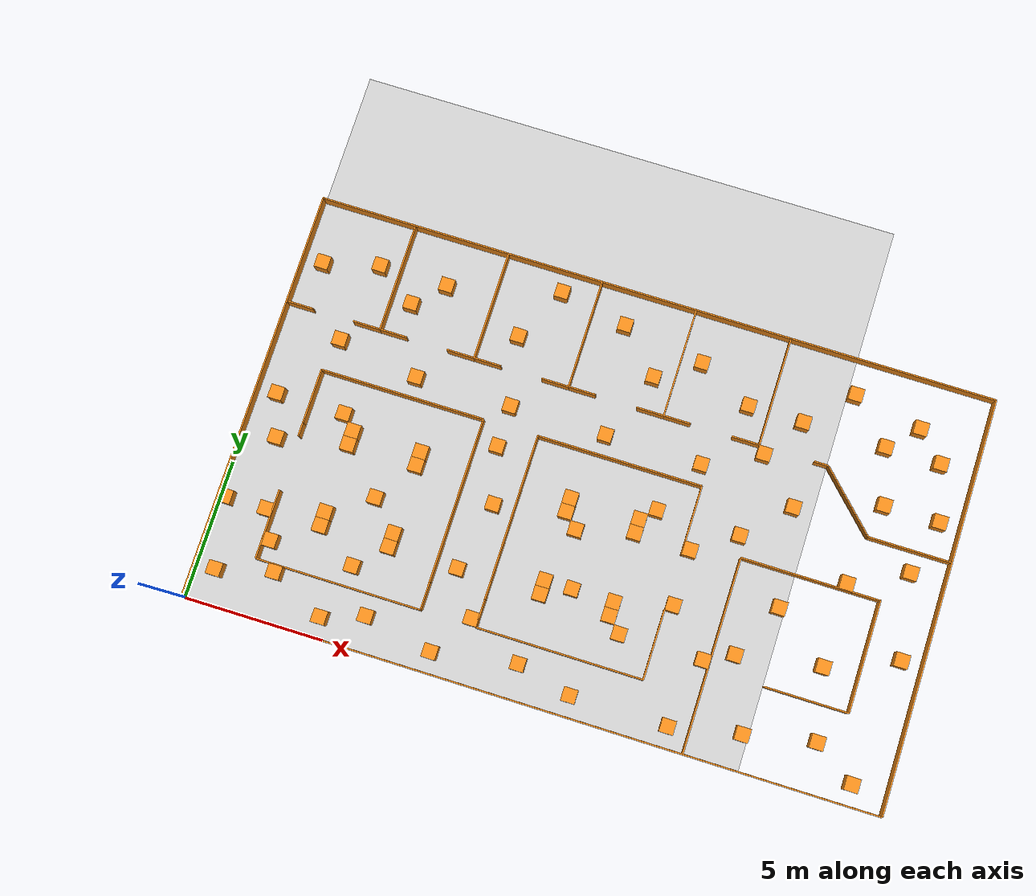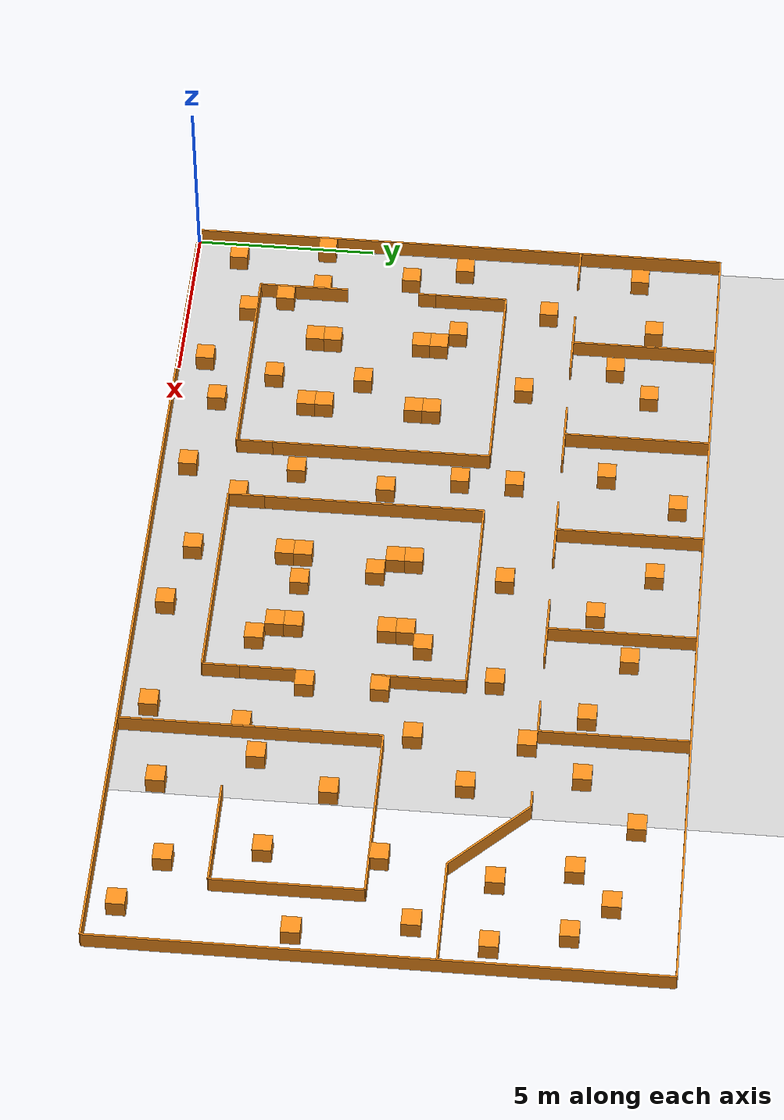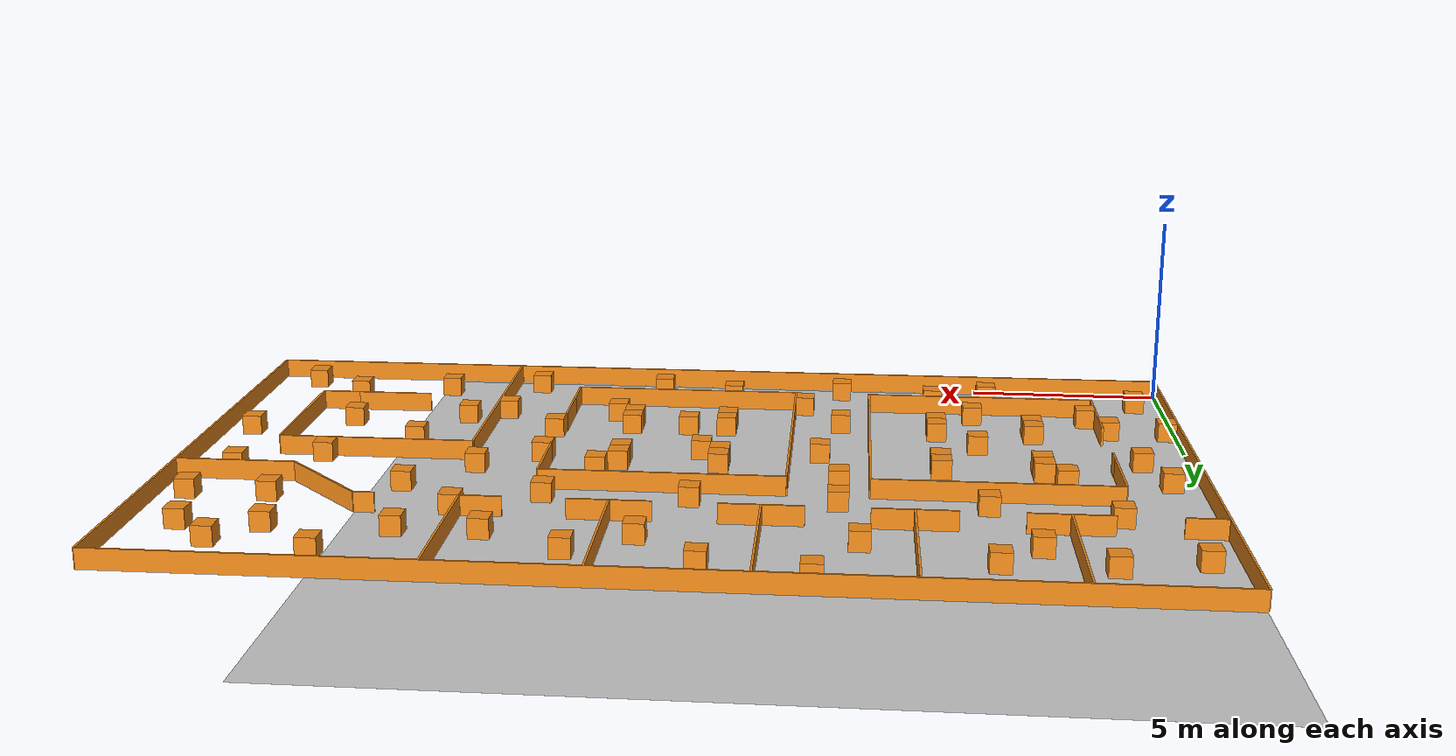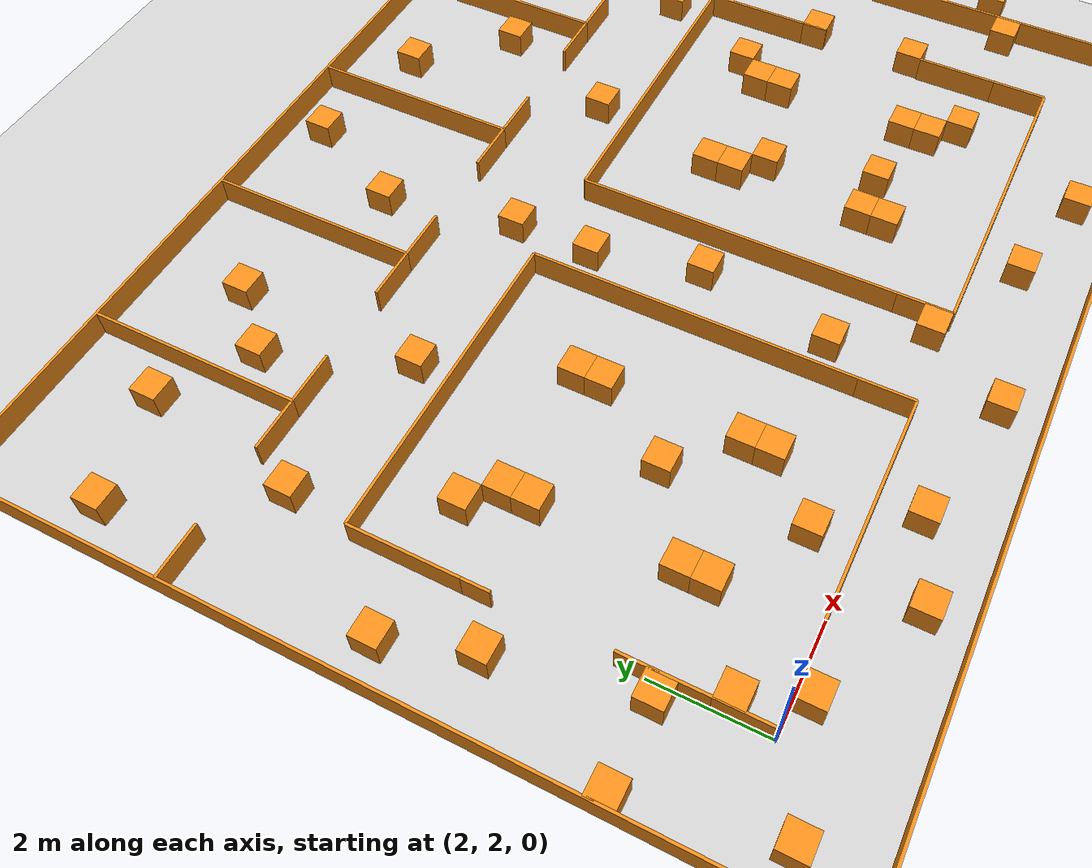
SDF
<sdf version="1.7">
 <world name="default">
  <model name="box_121">
   <pose>8.75 9.75 0.25 0 -0 0</pose>
   <link name="link">
    <inertial>
     <mass>1</mass>
     <inertia><ixx>0</ixx><ixy>0</ixy><ixz>0</ixz><iyy>0</iyy><iyz>0</iyz><izz>0</izz></inertia>
    </inertial>
    <collision name="collision"><geometry><box><size>0.5 0.5 0.5</size></box></geometry></collision>
    <visual name="visual">
     <geometry><box><size>0.5 0.5 0.5</size></box></geometry>
     <material>
      <script><name>Gazebo/Orange</name><uri>file://media/materials/scripts/gazebo.material</uri></script>
     </material>
    </visual>
   </link>
   <static>1</static>
  </model>
  <model name="box_120">
   <pose>16.25 6.75 0.25 0 -0 0</pose>
   <link name="link">
    <inertial>
     <mass>1</mass>
     <inertia><ixx>0</ixx><ixy>0</ixy><ixz>0</ixz><iyy>0</iyy><iyz>0</iyz><izz>0</izz></inertia>
    </inertial>
    <collision name="collision"><geometry><box><size>0.5 0.5 0.5</size></box></geometry></collision>
    <visual name="visual">
     <geometry><box><size>0.5 0.5 0.5</size></box></geometry>
     <material>
      <script><name>Gazebo/Orange</name><uri>file://media/materials/scripts/gazebo.material</uri></script>
     </material>
    </visual>
   </link>
   <static>1</static>
  </model>
  <model name="box_119">
   <pose>17.75 3.25 0.25 0 -0 0</pose>
   <link name="link">
    <inertial>
     <mass>1</mass>
     <inertia><ixx>0</ixx><ixy>0</ixy><ixz>0</ixz><iyy>0</iyy><iyz>0</iyz><izz>0</izz></inertia>
    </inertial>
    <collision name="collision"><geometry><box><size>0.5 0.5 0.5</size></box></geometry></collision>
    <visual name="visual">
     <geometry><box><size>0.5 0.5 0.5</size></box></geometry>
     <material>
      <script><name>Gazebo/Orange</name><uri>file://media/materials/scripts/gazebo.material</uri></script>
     </material>
    </visual>
   </link>
   <static>1</static>
  </model>
  <model name="box_118">
   <pose>9.75 2.25 0.25 0 -0 0</pose>
   <link name="link">
    <inertial>
     <mass>1</mass>
     <inertia><ixx>0</ixx><ixy>0</ixy><ixz>0</ixz><iyy>0</iyy><iyz>0</iyz><izz>0</izz></inertia>
    </inertial>
    <collision name="collision"><geometry><box><size>0.5 0.5 0.5</size></box></geometry></collision>
    <visual name="visual">
     <geometry><box><size>0.5 0.5 0.5</size></box></geometry>
     <material>
      <script><name>Gazebo/Orange</name><uri>file://media/materials/scripts/gazebo.material</uri></script>
     </material>
    </visual>
   </link>
   <static>1</static>
  </model>
  <model name="box_117">
   <pose>8.75 8.25 0.25 0 -0 0</pose>
   <link name="link">
    <inertial>
     <mass>1</mass>
     <inertia><ixx>0</ixx><ixy>0</ixy><ixz>0</ixz><iyy>0</iyy><iyz>0</iyz><izz>0</izz></inertia>
    </inertial>
    <collision name="collision"><geometry><box><size>0.5 0.5 0.5</size></box></geometry></collision>
    <visual name="visual">
     <geometry><box><size>0.5 0.5 0.5</size></box></geometry>
     <material>
      <script><name>Gazebo/Orange</name><uri>file://media/materials/scripts/gazebo.material</uri></script>
     </material>
    </visual>
   </link>
   <static>1</static>
  </model>
  <model name="box_116">
   <pose>8.75 3.75 0.25 0 -0 0</pose>
   <link name="link">
    <inertial>
     <mass>1</mass>
     <inertia><ixx>0</ixx><ixy>0</ixy><ixz>0</ixz><iyy>0</iyy><iyz>0</iyz><izz>0</izz></inertia>
    </inertial>
    <collision name="collision"><geometry><box><size>0.5 0.5 0.5</size></box></geometry></collision>
    <visual name="visual">
     <geometry><box><size>0.5 0.5 0.5</size></box></geometry>
     <material>
      <script><name>Gazebo/Orange</name><uri>file://media/materials/scripts/gazebo.material</uri></script>
     </material>
    </visual>
   </link>
   <static>1</static>
  </model>
  <model name="box_115">
   <pose>5.25 2.75 0.25 0 -0 0</pose>
   <link name="link">
    <inertial>
     <mass>1</mass>
     <inertia><ixx>0</ixx><ixy>0</ixy><ixz>0</ixz><iyy>0</iyy><iyz>0</iyz><izz>0</izz></inertia>
    </inertial>
    <collision name="collision"><geometry><box><size>0.5 0.5 0.5</size></box></geometry></collision>
    <visual name="visual">
     <geometry><box><size>0.5 0.5 0.5</size></box></geometry>
     <material>
      <script><name>Gazebo/Orange</name><uri>file://media/materials/scripts/gazebo.material</uri></script>
     </material>
    </visual>
   </link>
   <static>1</static>
  </model>
  <model name="box_114">
   <pose>2.25 2.75 0.25 0 -0 0</pose>
   <link name="link">
    <inertial>
     <mass>1</mass>
     <inertia><ixx>0</ixx><ixy>0</ixy><ixz>0</ixz><iyy>0</iyy><iyz>0</iyz><izz>0</izz></inertia>
    </inertial>
    <collision name="collision"><geometry><box><size>0.5 0.5 0.5</size></box></geometry></collision>
    <visual name="visual">
     <geometry><box><size>0.5 0.5 0.5</size></box></geometry>
     <material>
      <script><name>Gazebo/Orange</name><uri>file://media/materials/scripts/gazebo.material</uri></script>
     </material>
    </visual>
   </link>
   <static>1</static>
  </model>
  <model name="box_113">
   <pose>12.75 4.25 0.25 0 -0 0</pose>
   <link name="link">
    <inertial>
     <mass>1</mass>
     <inertia><ixx>0</ixx><ixy>0</ixy><ixz>0</ixz><iyy>0</iyy><iyz>0</iyz><izz>0</izz></inertia>
    </inertial>
    <collision name="collision"><geometry><box><size>0.5 0.5 0.5</size></box></geometry></collision>
    <visual name="visual">
     <geometry><box><size>0.5 0.5 0.5</size></box></geometry>
     <material>
      <script><name>Gazebo/Orange</name><uri>file://media/materials/scripts/gazebo.material</uri></script>
     </material>
    </visual>
   </link>
   <static>1</static>
  </model>
  <model name="box_112">
   <pose>14.75 3.25 0.25 0 -0 0</pose>
   <link name="link">
    <inertial>
     <mass>1</mass>
     <inertia><ixx>0</ixx><ixy>0</ixy><ixz>0</ixz><iyy>0</iyy><iyz>0</iyz><izz>0</izz></inertia>
    </inertial>
    <collision name="collision"><geometry><box><size>0.5 0.5 0.5</size></box></geometry></collision>
    <visual name="visual">
     <geometry><box><size>0.5 0.5 0.5</size></box></geometry>
     <material>
      <script><name>Gazebo/Orange</name><uri>file://media/materials/scripts/gazebo.material</uri></script>
     </material>
    </visual>
   </link>
   <static>1</static>
  </model>
  <model name="box_111">
   <pose>14.75 7.75 0.25 0 -0 0</pose>
   <link name="link">
    <inertial>
     <mass>1</mass>
     <inertia><ixx>0</ixx><ixy>0</ixy><ixz>0</ixz><iyy>0</iyy><iyz>0</iyz><izz>0</izz></inertia>
    </inertial>
    <collision name="collision"><geometry><box><size>0.5 0.5 0.5</size></box></geometry></collision>
    <visual name="visual">
     <geometry><box><size>0.5 0.5 0.5</size></box></geometry>
     <material>
      <script><name>Gazebo/Orange</name><uri>file://media/materials/scripts/gazebo.material</uri></script>
     </material>
    </visual>
   </link>
   <static>1</static>
  </model>
  <model name="box_110">
   <pose>3.25 7.75 0.25 0 -0 0</pose>
   <link name="link">
    <inertial>
     <mass>1</mass>
     <inertia><ixx>0</ixx><ixy>0</ixy><ixz>0</ixz><iyy>0</iyy><iyz>0</iyz><izz>0</izz></inertia>
    </inertial>
    <collision name="collision"><geometry><box><size>0.5 0.5 0.5</size></box></geometry></collision>
    <visual name="visual">
     <geometry><box><size>0.5 0.5 0.5</size></box></geometry>
     <material>
      <script><name>Gazebo/Orange</name><uri>file://media/materials/scripts/gazebo.material</uri></script>
     </material>
    </visual>
   </link>
   <static>1</static>
  </model>
  <model name="box_109">
   <pose>12.25 6.25 0.25 0 -0 0</pose>
   <link name="link">
    <inertial>
     <mass>1</mass>
     <inertia><ixx>0</ixx><ixy>0</ixy><ixz>0</ixz><iyy>0</iyy><iyz>0</iyz><izz>0</izz></inertia>
    </inertial>
    <collision name="collision"><geometry><box><size>0.5 0.5 0.5</size></box></geometry></collision>
    <visual name="visual">
     <geometry><box><size>0.5 0.5 0.5</size></box></geometry>
     <material>
      <script><name>Gazebo/Orange</name><uri>file://media/materials/scripts/gazebo.material</uri></script>
     </material>
    </visual>
   </link>
   <static>1</static>
  </model>
  <model name="box_108">
   <pose>5.25 5.25 0.25 0 -0 0</pose>
   <link name="link">
    <inertial>
     <mass>1</mass>
     <inertia><ixx>0</ixx><ixy>0</ixy><ixz>0</ixz><iyy>0</iyy><iyz>0</iyz><izz>0</izz></inertia>
    </inertial>
    <collision name="collision"><geometry><box><size>0.5 0.5 0.5</size></box></geometry></collision>
    <visual name="visual">
     <geometry><box><size>0.5 0.5 0.5</size></box></geometry>
     <material>
      <script><name>Gazebo/Orange</name><uri>file://media/materials/scripts/gazebo.material</uri></script>
     </material>
    </visual>
   </link>
   <static>1</static>
  </model>
  <model name="box_107">
   <pose>23.75 12.25 0.25 0 -0 0</pose>
   <link name="link">
    <inertial>
     <mass>1</mass>
     <inertia><ixx>0</ixx><ixy>0</ixy><ixz>0</ixz><iyy>0</iyy><iyz>0</iyz><izz>0</izz></inertia>
    </inertial>
    <collision name="collision"><geometry><box><size>0.5 0.5 0.5</size></box></geometry></collision>
    <visual name="visual">
     <geometry><box><size>0.5 0.5 0.5</size></box></geometry>
     <material>
      <script><name>Gazebo/Orange</name><uri>file://media/materials/scripts/gazebo.material</uri></script>
     </material>
    </visual>
   </link>
   <static>1</static>
  </model>
  <model name="box_106">
   <pose>23.75 8.25 0.25 0 -0 0</pose>
   <link name="link">
    <inertial>
     <mass>1</mass>
     <inertia><ixx>0</ixx><ixy>0</ixy><ixz>0</ixz><iyy>0</iyy><iyz>0</iyz><izz>0</izz></inertia>
    </inertial>
    <collision name="collision"><geometry><box><size>0.5 0.5 0.5</size></box></geometry></collision>
    <visual name="visual">
     <geometry><box><size>0.5 0.5 0.5</size></box></geometry>
     <material>
      <script><name>Gazebo/Orange</name><uri>file://media/materials/scripts/gazebo.material</uri></script>
     </material>
    </visual>
   </link>
   <static>1</static>
  </model>
  <model name="box_105">
   <pose>23.75 0.75 0.25 0 -0 0</pose>
   <link name="link">
    <inertial>
     <mass>1</mass>
     <inertia><ixx>0</ixx><ixy>0</ixy><ixz>0</ixz><iyy>0</iyy><iyz>0</iyz><izz>0</izz></inertia>
    </inertial>
    <collision name="collision"><geometry><box><size>0.5 0.5 0.5</size></box></geometry></collision>
    <visual name="visual">
     <geometry><box><size>0.5 0.5 0.5</size></box></geometry>
     <material>
      <script><name>Gazebo/Orange</name><uri>file://media/materials/scripts/gazebo.material</uri></script>
     </material>
    </visual>
   </link>
   <static>1</static>
  </model>
  <model name="box_104">
   <pose>24.25 5.25 0.25 0 -0 0</pose>
   <link name="link">
    <inertial>
     <mass>1</mass>
     <inertia><ixx>0</ixx><ixy>0</ixy><ixz>0</ixz><iyy>0</iyy><iyz>0</iyz><izz>0</izz></inertia>
    </inertial>
    <collision name="collision"><geometry><box><size>0.5 0.5 0.5</size></box></geometry></collision>
    <visual name="visual">
     <geometry><box><size>0.5 0.5 0.5</size></box></geometry>
     <material>
      <script><name>Gazebo/Orange</name><uri>file://media/materials/scripts/gazebo.material</uri></script>
     </material>
    </visual>
   </link>
   <static>1</static>
  </model>
  <model name="box_103">
   <pose>18.75 3.75 0.25 0 -0 0</pose>
   <link name="link">
    <inertial>
     <mass>1</mass>
     <inertia><ixx>0</ixx><ixy>0</ixy><ixz>0</ixz><iyy>0</iyy><iyz>0</iyz><izz>0</izz></inertia>
    </inertial>
    <collision name="collision"><geometry><box><size>0.5 0.5 0.5</size></box></geometry></collision>
    <visual name="visual">
     <geometry><box><size>0.5 0.5 0.5</size></box></geometry>
     <material>
      <script><name>Gazebo/Orange</name><uri>file://media/materials/scripts/gazebo.material</uri></script>
     </material>
    </visual>
   </link>
   <static>1</static>
  </model>
  <model name="box_102">
   <pose>6.25 1.25 0.25 0 -0 0</pose>
   <link name="link">
    <inertial>
     <mass>1</mass>
     <inertia><ixx>0</ixx><ixy>0</ixy><ixz>0</ixz><iyy>0</iyy><iyz>0</iyz><izz>0</izz></inertia>
    </inertial>
    <collision name="collision"><geometry><box><size>0.5 0.5 0.5</size></box></geometry></collision>
    <visual name="visual">
     <geometry><box><size>0.5 0.5 0.5</size></box></geometry>
     <material>
      <script><name>Gazebo/Orange</name><uri>file://media/materials/scripts/gazebo.material</uri></script>
     </material>
    </visual>
   </link>
   <static>1</static>
  </model>
  <model name="box_101">
   <pose>2.75 1.75 0.25 0 -0 0</pose>
   <link name="link">
    <inertial>
     <mass>1</mass>
     <inertia><ixx>0</ixx><ixy>0</ixy><ixz>0</ixz><iyy>0</iyy><iyz>0</iyz><izz>0</izz></inertia>
    </inertial>
    <collision name="collision"><geometry><box><size>0.5 0.5 0.5</size></box></geometry></collision>
    <visual name="visual">
     <geometry><box><size>0.5 0.5 0.5</size></box></geometry>
     <material>
      <script><name>Gazebo/Orange</name><uri>file://media/materials/scripts/gazebo.material</uri></script>
     </material>
    </visual>
   </link>
   <static>1</static>
  </model>
  <model name="box_100">
   <pose>4.75 0.75 0.25 0 -0 0</pose>
   <link name="link">
    <inertial>
     <mass>1</mass>
     <inertia><ixx>0</ixx><ixy>0</ixy><ixz>0</ixz><iyy>0</iyy><iyz>0</iyz><izz>0</izz></inertia>
    </inertial>
    <collision name="collision"><geometry><box><size>0.5 0.5 0.5</size></box></geometry></collision>
    <visual name="visual">
     <geometry><box><size>0.5 0.5 0.5</size></box></geometry>
     <material>
      <script><name>Gazebo/Orange</name><uri>file://media/materials/scripts/gazebo.material</uri></script>
     </material>
    </visual>
   </link>
   <static>1</static>
  </model>
  <model name="box_99">
   <pose>1.25 6.25 0.25 0 -0 0</pose>
   <link name="link">
    <inertial>
     <mass>1</mass>
     <inertia><ixx>0</ixx><ixy>0</ixy><ixz>0</ixz><iyy>0</iyy><iyz>0</iyz><izz>0</izz></inertia>
    </inertial>
    <collision name="collision"><geometry><box><size>0.5 0.5 0.5</size></box></geometry></collision>
    <visual name="visual">
     <geometry><box><size>0.5 0.5 0.5</size></box></geometry>
     <material>
      <script><name>Gazebo/Orange</name><uri>file://media/materials/scripts/gazebo.material</uri></script>
     </material>
    </visual>
   </link>
   <static>1</static>
  </model>
  <model name="box_98">
   <pose>1.75 3.75 0.25 0 -0 0</pose>
   <link name="link">
    <inertial>
     <mass>1</mass>
     <inertia><ixx>0</ixx><ixy>0</ixy><ixz>0</ixz><iyy>0</iyy><iyz>0</iyz><izz>0</izz></inertia>
    </inertial>
    <collision name="collision"><geometry><box><size>0.5 0.5 0.5</size></box></geometry></collision>
    <visual name="visual">
     <geometry><box><size>0.5 0.5 0.5</size></box></geometry>
     <material>
      <script><name>Gazebo/Orange</name><uri>file://media/materials/scripts/gazebo.material</uri></script>
     </material>
    </visual>
   </link>
   <static>1</static>
  </model>
  <model name="box_97">
   <pose>0.25 3.75 0.25 0 -0 0</pose>
   <link name="link">
    <inertial>
     <mass>1</mass>
     <inertia><ixx>0</ixx><ixy>0</ixy><ixz>0</ixz><iyy>0</iyy><iyz>0</iyz><izz>0</izz></inertia>
    </inertial>
    <collision name="collision"><geometry><box><size>0.5 0.5 0.5</size></box></geometry></collision>
    <visual name="visual">
     <geometry><box><size>0.5 0.5 0.5</size></box></geometry>
     <material>
      <script><name>Gazebo/Orange</name><uri>file://media/materials/scripts/gazebo.material</uri></script>
     </material>
    </visual>
   </link>
   <static>1</static>
  </model>
  <model name="box_96">
   <pose>5.25 9.75 0.25 0 -0 0</pose>
   <link name="link">
    <inertial>
     <mass>1</mass>
     <inertia><ixx>0</ixx><ixy>0</ixy><ixz>0</ixz><iyy>0</iyy><iyz>0</iyz><izz>0</izz></inertia>
    </inertial>
    <collision name="collision"><geometry><box><size>0.5 0.5 0.5</size></box></geometry></collision>
    <visual name="visual">
     <geometry><box><size>0.5 0.5 0.5</size></box></geometry>
     <material>
      <script><name>Gazebo/Orange</name><uri>file://media/materials/scripts/gazebo.material</uri></script>
     </material>
    </visual>
   </link>
   <static>1</static>
  </model>
  <model name="box_95">
   <pose>2.25 10.25 0.25 0 -0 0</pose>
   <link name="link">
    <inertial>
     <mass>1</mass>
     <inertia><ixx>0</ixx><ixy>0</ixy><ixz>0</ixz><iyy>0</iyy><iyz>0</iyz><izz>0</izz></inertia>
    </inertial>
    <collision name="collision"><geometry><box><size>0.5 0.5 0.5</size></box></geometry></collision>
    <visual name="visual">
     <geometry><box><size>0.5 0.5 0.5</size></box></geometry>
     <material>
      <script><name>Gazebo/Orange</name><uri>file://media/materials/scripts/gazebo.material</uri></script>
     </material>
    </visual>
   </link>
   <static>1</static>
  </model>
  <model name="box_94">
   <pose>0.75 7.75 0.25 0 -0 0</pose>
   <link name="link">
    <inertial>
     <mass>1</mass>
     <inertia><ixx>0</ixx><ixy>0</ixy><ixz>0</ixz><iyy>0</iyy><iyz>0</iyz><izz>0</izz></inertia>
    </inertial>
    <collision name="collision"><geometry><box><size>0.5 0.5 0.5</size></box></geometry></collision>
    <visual name="visual">
     <geometry><box><size>0.5 0.5 0.5</size></box></geometry>
     <material>
      <script><name>Gazebo/Orange</name><uri>file://media/materials/scripts/gazebo.material</uri></script>
     </material>
    </visual>
   </link>
   <static>1</static>
  </model>
  <model name="box_93">
   <pose>13.75 0.75 0.25 0 -0 0</pose>
   <link name="link">
    <inertial>
     <mass>1</mass>
     <inertia><ixx>0</ixx><ixy>0</ixy><ixz>0</ixz><iyy>0</iyy><iyz>0</iyz><izz>0</izz></inertia>
    </inertial>
    <collision name="collision"><geometry><box><size>0.5 0.5 0.5</size></box></geometry></collision>
    <visual name="visual">
     <geometry><box><size>0.5 0.5 0.5</size></box></geometry>
     <material>
      <script><name>Gazebo/Orange</name><uri>file://media/materials/scripts/gazebo.material</uri></script>
     </material>
    </visual>
   </link>
   <static>1</static>
  </model>
  <model name="box_92">
   <pose>11.75 1.25 0.25 0 -0 0</pose>
   <link name="link">
    <inertial>
     <mass>1</mass>
     <inertia><ixx>0</ixx><ixy>0</ixy><ixz>0</ixz><iyy>0</iyy><iyz>0</iyz><izz>0</izz></inertia>
    </inertial>
    <collision name="collision"><geometry><box><size>0.5 0.5 0.5</size></box></geometry></collision>
    <visual name="visual">
     <geometry><box><size>0.5 0.5 0.5</size></box></geometry>
     <material>
      <script><name>Gazebo/Orange</name><uri>file://media/materials/scripts/gazebo.material</uri></script>
     </material>
    </visual>
   </link>
   <static>1</static>
  </model>
  <model name="box_91">
   <pose>17.25 0.75 0.25 0 -0 0</pose>
   <link name="link">
    <inertial>
     <mass>1</mass>
     <inertia><ixx>0</ixx><ixy>0</ixy><ixz>0</ixz><iyy>0</iyy><iyz>0</iyz><izz>0</izz></inertia>
    </inertial>
    <collision name="collision"><geometry><box><size>0.5 0.5 0.5</size></box></geometry></collision>
    <visual name="visual">
     <geometry><box><size>0.5 0.5 0.5</size></box></geometry>
     <material>
      <script><name>Gazebo/Orange</name><uri>file://media/materials/scripts/gazebo.material</uri></script>
     </material>
    </visual>
   </link>
   <static>1</static>
  </model>
  <model name="box_90">
   <pose>16.25 4.75 0.25 0 -0 0</pose>
   <link name="link">
    <inertial>
     <mass>1</mass>
     <inertia><ixx>0</ixx><ixy>0</ixy><ixz>0</ixz><iyy>0</iyy><iyz>0</iyz><izz>0</izz></inertia>
    </inertial>
    <collision name="collision"><geometry><box><size>0.5 0.5 0.5</size></box></geometry></collision>
    <visual name="visual">
     <geometry><box><size>0.5 0.5 0.5</size></box></geometry>
     <material>
      <script><name>Gazebo/Orange</name><uri>file://media/materials/scripts/gazebo.material</uri></script>
     </material>
    </visual>
   </link>
   <static>1</static>
  </model>
  <model name="box_89">
   <pose>21.75 7.25 0.25 0 -0 0</pose>
   <link name="link">
    <inertial>
     <mass>1</mass>
     <inertia><ixx>0</ixx><ixy>0</ixy><ixz>0</ixz><iyy>0</iyy><iyz>0</iyz><izz>0</izz></inertia>
    </inertial>
    <collision name="collision"><geometry><box><size>0.5 0.5 0.5</size></box></geometry></collision>
    <visual name="visual">
     <geometry><box><size>0.5 0.5 0.5</size></box></geometry>
     <material>
      <script><name>Gazebo/Orange</name><uri>file://media/materials/scripts/gazebo.material</uri></script>
     </material>
    </visual>
   </link>
   <static>1</static>
  </model>
  <model name="box_88">
   <pose>17.75 10.75 0.25 0 -0 0</pose>
   <link name="link">
    <inertial>
     <mass>1</mass>
     <inertia><ixx>0</ixx><ixy>0</ixy><ixz>0</ixz><iyy>0</iyy><iyz>0</iyz><izz>0</izz></inertia>
    </inertial>
    <collision name="collision"><geometry><box><size>0.5 0.5 0.5</size></box></geometry></collision>
    <visual name="visual">
     <geometry><box><size>0.5 0.5 0.5</size></box></geometry>
     <material>
      <script><name>Gazebo/Orange</name><uri>file://media/materials/scripts/gazebo.material</uri></script>
     </material>
    </visual>
   </link>
   <static>1</static>
  </model>
  <model name="box_87">
   <pose>15.75 9.75 0.25 0 -0 0</pose>
   <link name="link">
    <inertial>
     <mass>1</mass>
     <inertia><ixx>0</ixx><ixy>0</ixy><ixz>0</ixz><iyy>0</iyy><iyz>0</iyz><izz>0</izz></inertia>
    </inertial>
    <collision name="collision"><geometry><box><size>0.5 0.5 0.5</size></box></geometry></collision>
    <visual name="visual">
     <geometry><box><size>0.5 0.5 0.5</size></box></geometry>
     <material>
      <script><name>Gazebo/Orange</name><uri>file://media/materials/scripts/gazebo.material</uri></script>
     </material>
    </visual>
   </link>
   <static>1</static>
  </model>
  <model name="box_86">
   <pose>12.25 9.75 0.25 0 -0 0</pose>
   <link name="link">
    <inertial>
     <mass>1</mass>
     <inertia><ixx>0</ixx><ixy>0</ixy><ixz>0</ixz><iyy>0</iyy><iyz>0</iyz><izz>0</izz></inertia>
    </inertial>
    <collision name="collision"><geometry><box><size>0.5 0.5 0.5</size></box></geometry></collision>
    <visual name="visual">
     <geometry><box><size>0.5 0.5 0.5</size></box></geometry>
     <material>
      <script><name>Gazebo/Orange</name><uri>file://media/materials/scripts/gazebo.material</uri></script>
     </material>
    </visual>
   </link>
   <static>1</static>
  </model>
  <model name="box_85">
   <pose>9.25 6.25 0.25 0 -0 0</pose>
   <link name="link">
    <inertial>
     <mass>1</mass>
     <inertia><ixx>0</ixx><ixy>0</ixy><ixz>0</ixz><iyy>0</iyy><iyz>0</iyz><izz>0</izz></inertia>
    </inertial>
    <collision name="collision"><geometry><box><size>0.5 0.5 0.5</size></box></geometry></collision>
    <visual name="visual">
     <geometry><box><size>0.5 0.5 0.5</size></box></geometry>
     <material>
      <script><name>Gazebo/Orange</name><uri>file://media/materials/scripts/gazebo.material</uri></script>
     </material>
    </visual>
   </link>
   <static>1</static>
  </model>
  <model name="box_84">
   <pose>8.75 0.75 0.25 0 -0 0</pose>
   <link name="link">
    <inertial>
     <mass>1</mass>
     <inertia><ixx>0</ixx><ixy>0</ixy><ixz>0</ixz><iyy>0</iyy><iyz>0</iyz><izz>0</izz></inertia>
    </inertial>
    <collision name="collision"><geometry><box><size>0.5 0.5 0.5</size></box></geometry></collision>
    <visual name="visual">
     <geometry><box><size>0.5 0.5 0.5</size></box></geometry>
     <material>
      <script><name>Gazebo/Orange</name><uri>file://media/materials/scripts/gazebo.material</uri></script>
     </material>
    </visual>
   </link>
   <static>1</static>
  </model>
  <model name="box_83">
   <pose>0.75 1.25 0.25 0 -0 0</pose>
   <link name="link">
    <inertial>
     <mass>1</mass>
     <inertia><ixx>0</ixx><ixy>0</ixy><ixz>0</ixz><iyy>0</iyy><iyz>0</iyz><izz>0</izz></inertia>
    </inertial>
    <collision name="collision"><geometry><box><size>0.5 0.5 0.5</size></box></geometry></collision>
    <visual name="visual">
     <geometry><box><size>0.5 0.5 0.5</size></box></geometry>
     <material>
      <script><name>Gazebo/Orange</name><uri>file://media/materials/scripts/gazebo.material</uri></script>
     </material>
    </visual>
   </link>
   <static>1</static>
  </model>
  <model name="box_82">
   <pose>22.25 1.75 0.25 0 -0 0</pose>
   <link name="link">
    <inertial>
     <mass>1</mass>
     <inertia><ixx>0</ixx><ixy>0</ixy><ixz>0</ixz><iyy>0</iyy><iyz>0</iyz><izz>0</izz></inertia>
    </inertial>
    <collision name="collision"><geometry><box><size>0.5 0.5 0.5</size></box></geometry></collision>
    <visual name="visual">
     <geometry><box><size>0.5 0.5 0.5</size></box></geometry>
     <material>
      <script><name>Gazebo/Orange</name><uri>file://media/materials/scripts/gazebo.material</uri></script>
     </material>
    </visual>
   </link>
   <static>1</static>
  </model>
  <model name="box_81">
   <pose>19.75 1.25 0.25 0 -0 0</pose>
   <link name="link">
    <inertial>
     <mass>1</mass>
     <inertia><ixx>0</ixx><ixy>0</ixy><ixz>0</ixz><iyy>0</iyy><iyz>0</iyz><izz>0</izz></inertia>
    </inertial>
    <collision name="collision"><geometry><box><size>0.5 0.5 0.5</size></box></geometry></collision>
    <visual name="visual">
     <geometry><box><size>0.5 0.5 0.5</size></box></geometry>
     <material>
      <script><name>Gazebo/Orange</name><uri>file://media/materials/scripts/gazebo.material</uri></script>
     </material>
    </visual>
   </link>
   <static>1</static>
  </model>
  <model name="box_80">
   <pose>21.75 4.25 0.25 0 -0 0</pose>
   <link name="link">
    <inertial>
     <mass>1</mass>
     <inertia><ixx>0</ixx><ixy>0</ixy><ixz>0</ixz><iyy>0</iyy><iyz>0</iyz><izz>0</izz></inertia>
    </inertial>
    <collision name="collision"><geometry><box><size>0.5 0.5 0.5</size></box></geometry></collision>
    <visual name="visual">
     <geometry><box><size>0.5 0.5 0.5</size></box></geometry>
     <material>
      <script><name>Gazebo/Orange</name><uri>file://media/materials/scripts/gazebo.material</uri></script>
     </material>
    </visual>
   </link>
   <static>1</static>
  </model>
  <model name="box_79">
   <pose>19.75 5.75 0.25 0 -0 0</pose>
   <link name="link">
    <inertial>
     <mass>1</mass>
     <inertia><ixx>0</ixx><ixy>0</ixy><ixz>0</ixz><iyy>0</iyy><iyz>0</iyz><izz>0</izz></inertia>
    </inertial>
    <collision name="collision"><geometry><box><size>0.5 0.5 0.5</size></box></geometry></collision>
    <visual name="visual">
     <geometry><box><size>0.5 0.5 0.5</size></box></geometry>
     <material>
      <script><name>Gazebo/Orange</name><uri>file://media/materials/scripts/gazebo.material</uri></script>
     </material>
    </visual>
   </link>
   <static>1</static>
  </model>
  <model name="box_78">
   <pose>17.75 7.75 0.25 0 -0 0</pose>
   <link name="link">
    <inertial>
     <mass>1</mass>
     <inertia><ixx>0</ixx><ixy>0</ixy><ixz>0</ixz><iyy>0</iyy><iyz>0</iyz><izz>0</izz></inertia>
    </inertial>
    <collision name="collision"><geometry><box><size>0.5 0.5 0.5</size></box></geometry></collision>
    <visual name="visual">
     <geometry><box><size>0.5 0.5 0.5</size></box></geometry>
     <material>
      <script><name>Gazebo/Orange</name><uri>file://media/materials/scripts/gazebo.material</uri></script>
     </material>
    </visual>
   </link>
   <static>1</static>
  </model>
  <model name="box_77">
   <pose>19.25 9.25 0.25 0 -0 0</pose>
   <link name="link">
    <inertial>
     <mass>1</mass>
     <inertia><ixx>0</ixx><ixy>0</ixy><ixz>0</ixz><iyy>0</iyy><iyz>0</iyz><izz>0</izz></inertia>
    </inertial>
    <collision name="collision"><geometry><box><size>0.5 0.5 0.5</size></box></geometry></collision>
    <visual name="visual">
     <geometry><box><size>0.5 0.5 0.5</size></box></geometry>
     <material>
      <script><name>Gazebo/Orange</name><uri>file://media/materials/scripts/gazebo.material</uri></script>
     </material>
    </visual>
   </link>
   <static>1</static>
  </model>
  <model name="box_76">
   <pose>21.75 12.25 0.25 0 -0 0</pose>
   <link name="link">
    <inertial>
     <mass>1</mass>
     <inertia><ixx>0</ixx><ixy>0</ixy><ixz>0</ixz><iyy>0</iyy><iyz>0</iyz><izz>0</izz></inertia>
    </inertial>
    <collision name="collision"><geometry><box><size>0.5 0.5 0.5</size></box></geometry></collision>
    <visual name="visual">
     <geometry><box><size>0.5 0.5 0.5</size></box></geometry>
     <material>
      <script><name>Gazebo/Orange</name><uri>file://media/materials/scripts/gazebo.material</uri></script>
     </material>
    </visual>
   </link>
   <static>1</static>
  </model>
  <model name="box_75">
   <pose>22.25 10.25 0.25 0 -0 0</pose>
   <link name="link">
    <inertial>
     <mass>1</mass>
     <inertia><ixx>0</ixx><ixy>0</ixy><ixz>0</ixz><iyy>0</iyy><iyz>0</iyz><izz>0</izz></inertia>
    </inertial>
    <collision name="collision"><geometry><box><size>0.5 0.5 0.5</size></box></geometry></collision>
    <visual name="visual">
     <geometry><box><size>0.5 0.5 0.5</size></box></geometry>
     <material>
      <script><name>Gazebo/Orange</name><uri>file://media/materials/scripts/gazebo.material</uri></script>
     </material>
    </visual>
   </link>
   <static>1</static>
  </model>
  <model name="box_74">
   <pose>24.25 10.25 0.25 0 -0 0</pose>
   <link name="link">
    <inertial>
     <mass>1</mass>
     <inertia><ixx>0</ixx><ixy>0</ixy><ixz>0</ixz><iyy>0</iyy><iyz>0</iyz><izz>0</izz></inertia>
    </inertial>
    <collision name="collision"><geometry><box><size>0.5 0.5 0.5</size></box></geometry></collision>
    <visual name="visual">
     <geometry><box><size>0.5 0.5 0.5</size></box></geometry>
     <material>
      <script><name>Gazebo/Orange</name><uri>file://media/materials/scripts/gazebo.material</uri></script>
     </material>
    </visual>
   </link>
   <static>1</static>
  </model>
  <model name="box_73">
   <pose>18.75 12.25 0.25 0 -0 0</pose>
   <link name="link">
    <inertial>
     <mass>1</mass>
     <inertia><ixx>0</ixx><ixy>0</ixy><ixz>0</ixz><iyy>0</iyy><iyz>0</iyz><izz>0</izz></inertia>
    </inertial>
    <collision name="collision"><geometry><box><size>0.5 0.5 0.5</size></box></geometry></collision>
    <visual name="visual">
     <geometry><box><size>0.5 0.5 0.5</size></box></geometry>
     <material>
      <script><name>Gazebo/Orange</name><uri>file://media/materials/scripts/gazebo.material</uri></script>
     </material>
    </visual>
   </link>
   <static>1</static>
  </model>
  <model name="box_72">
   <pose>20.25 13.75 0.25 0 -0 0</pose>
   <link name="link">
    <inertial>
     <mass>1</mass>
     <inertia><ixx>0</ixx><ixy>0</ixy><ixz>0</ixz><iyy>0</iyy><iyz>0</iyz><izz>0</izz></inertia>
    </inertial>
    <collision name="collision"><geometry><box><size>0.5 0.5 0.5</size></box></geometry></collision>
    <visual name="visual">
     <geometry><box><size>0.5 0.5 0.5</size></box></geometry>
     <material>
      <script><name>Gazebo/Orange</name><uri>file://media/materials/scripts/gazebo.material</uri></script>
     </material>
    </visual>
   </link>
   <static>1</static>
  </model>
  <model name="box_71">
   <pose>22.75 13.25 0.25 0 -0 0</pose>
   <link name="link">
    <inertial>
     <mass>1</mass>
     <inertia><ixx>0</ixx><ixy>0</ixy><ixz>0</ixz><iyy>0</iyy><iyz>0</iyz><izz>0</izz></inertia>
    </inertial>
    <collision name="collision"><geometry><box><size>0.5 0.5 0.5</size></box></geometry></collision>
    <visual name="visual">
     <geometry><box><size>0.5 0.5 0.5</size></box></geometry>
     <material>
      <script><name>Gazebo/Orange</name><uri>file://media/materials/scripts/gazebo.material</uri></script>
     </material>
    </visual>
   </link>
   <static>1</static>
  </model>
  <model name="box_70">
   <pose>16.75 12.25 0.25 0 -0 0</pose>
   <link name="link">
    <inertial>
     <mass>1</mass>
     <inertia><ixx>0</ixx><ixy>0</ixy><ixz>0</ixz><iyy>0</iyy><iyz>0</iyz><izz>0</izz></inertia>
    </inertial>
    <collision name="collision"><geometry><box><size>0.5 0.5 0.5</size></box></geometry></collision>
    <visual name="visual">
     <geometry><box><size>0.5 0.5 0.5</size></box></geometry>
     <material>
      <script><name>Gazebo/Orange</name><uri>file://media/materials/scripts/gazebo.material</uri></script>
     </material>
    </visual>
   </link>
   <static>1</static>
  </model>
  <model name="box_69">
   <pose>14.75 13.25 0.25 0 -0 0</pose>
   <link name="link">
    <inertial>
     <mass>1</mass>
     <inertia><ixx>0</ixx><ixy>0</ixy><ixz>0</ixz><iyy>0</iyy><iyz>0</iyz><izz>0</izz></inertia>
    </inertial>
    <collision name="collision"><geometry><box><size>0.5 0.5 0.5</size></box></geometry></collision>
    <visual name="visual">
     <geometry><box><size>0.5 0.5 0.5</size></box></geometry>
     <material>
      <script><name>Gazebo/Orange</name><uri>file://media/materials/scripts/gazebo.material</uri></script>
     </material>
    </visual>
   </link>
   <static>1</static>
  </model>
  <model name="box_68">
   <pose>11.75 13.75 0.25 0 -0 0</pose>
   <link name="link">
    <inertial>
     <mass>1</mass>
     <inertia><ixx>0</ixx><ixy>0</ixy><ixz>0</ixz><iyy>0</iyy><iyz>0</iyz><izz>0</izz></inertia>
    </inertial>
    <collision name="collision"><geometry><box><size>0.5 0.5 0.5</size></box></geometry></collision>
    <visual name="visual">
     <geometry><box><size>0.5 0.5 0.5</size></box></geometry>
     <material>
      <script><name>Gazebo/Orange</name><uri>file://media/materials/scripts/gazebo.material</uri></script>
     </material>
    </visual>
   </link>
   <static>1</static>
  </model>
  <model name="box_67">
   <pose>13.25 12.25 0.25 0 -0 0</pose>
   <link name="link">
    <inertial>
     <mass>1</mass>
     <inertia><ixx>0</ixx><ixy>0</ixy><ixz>0</ixz><iyy>0</iyy><iyz>0</iyz><izz>0</izz></inertia>
    </inertial>
    <collision name="collision"><geometry><box><size>0.5 0.5 0.5</size></box></geometry></collision>
    <visual name="visual">
     <geometry><box><size>0.5 0.5 0.5</size></box></geometry>
     <material>
      <script><name>Gazebo/Orange</name><uri>file://media/materials/scripts/gazebo.material</uri></script>
     </material>
    </visual>
   </link>
   <static>1</static>
  </model>
  <model name="box_66">
   <pose>9.25 14.25 0.25 0 -0 0</pose>
   <link name="link">
    <inertial>
     <mass>1</mass>
     <inertia><ixx>0</ixx><ixy>0</ixy><ixz>0</ixz><iyy>0</iyy><iyz>0</iyz><izz>0</izz></inertia>
    </inertial>
    <collision name="collision"><geometry><box><size>0.5 0.5 0.5</size></box></geometry></collision>
    <visual name="visual">
     <geometry><box><size>0.5 0.5 0.5</size></box></geometry>
     <material>
      <script><name>Gazebo/Orange</name><uri>file://media/materials/scripts/gazebo.material</uri></script>
     </material>
    </visual>
   </link>
   <static>1</static>
  </model>
  <model name="box_65">
   <pose>8.25 12.25 0.25 0 -0 0</pose>
   <link name="link">
    <inertial>
     <mass>1</mass>
     <inertia><ixx>0</ixx><ixy>0</ixy><ixz>0</ixz><iyy>0</iyy><iyz>0</iyz><izz>0</izz></inertia>
    </inertial>
    <collision name="collision"><geometry><box><size>0.5 0.5 0.5</size></box></geometry></collision>
    <visual name="visual">
     <geometry><box><size>0.5 0.5 0.5</size></box></geometry>
     <material>
      <script><name>Gazebo/Orange</name><uri>file://media/materials/scripts/gazebo.material</uri></script>
     </material>
    </visual>
   </link>
   <static>1</static>
  </model>
  <model name="box_64">
   <pose>2.75 13.25 0.25 0 -0 0</pose>
   <link name="link">
    <inertial>
     <mass>1</mass>
     <inertia><ixx>0</ixx><ixy>0</ixy><ixz>0</ixz><iyy>0</iyy><iyz>0</iyz><izz>0</izz></inertia>
    </inertial>
    <collision name="collision"><geometry><box><size>0.5 0.5 0.5</size></box></geometry></collision>
    <visual name="visual">
     <geometry><box><size>0.5 0.5 0.5</size></box></geometry>
     <material>
      <script><name>Gazebo/Orange</name><uri>file://media/materials/scripts/gazebo.material</uri></script>
     </material>
    </visual>
   </link>
   <static>1</static>
  </model>
  <model name="box_63">
   <pose>0.75 12.75 0.25 0 -0 0</pose>
   <link name="link">
    <inertial>
     <mass>1</mass>
     <inertia><ixx>0</ixx><ixy>0</ixy><ixz>0</ixz><iyy>0</iyy><iyz>0</iyz><izz>0</izz></inertia>
    </inertial>
    <collision name="collision"><geometry><box><size>0.5 0.5 0.5</size></box></geometry></collision>
    <visual name="visual">
     <geometry><box><size>0.5 0.5 0.5</size></box></geometry>
     <material>
      <script><name>Gazebo/Orange</name><uri>file://media/materials/scripts/gazebo.material</uri></script>
     </material>
    </visual>
   </link>
   <static>1</static>
  </model>
  <model name="box_62">
   <pose>4.25 12.25 0.25 0 -0 0</pose>
   <link name="link">
    <inertial>
     <mass>1</mass>
     <inertia><ixx>0</ixx><ixy>0</ixy><ixz>0</ixz><iyy>0</iyy><iyz>0</iyz><izz>0</izz></inertia>
    </inertial>
    <collision name="collision"><geometry><box><size>0.5 0.5 0.5</size></box></geometry></collision>
    <visual name="visual">
     <geometry><box><size>0.5 0.5 0.5</size></box></geometry>
     <material>
      <script><name>Gazebo/Orange</name><uri>file://media/materials/scripts/gazebo.material</uri></script>
     </material>
    </visual>
   </link>
   <static>1</static>
  </model>
  <model name="box_61">
   <pose>5.25 13.25 0.25 0 -0 0</pose>
   <link name="link">
    <inertial>
     <mass>1</mass>
     <inertia><ixx>0</ixx><ixy>0</ixy><ixz>0</ixz><iyy>0</iyy><iyz>0</iyz><izz>0</izz></inertia>
    </inertial>
    <collision name="collision"><geometry><box><size>0.5 0.5 0.5</size></box></geometry></collision>
    <visual name="visual">
     <geometry><box><size>0.5 0.5 0.5</size></box></geometry>
     <material>
      <script><name>Gazebo/Orange</name><uri>file://media/materials/scripts/gazebo.material</uri></script>
     </material>
    </visual>
   </link>
   <static>1</static>
  </model>
  <model name="box_60">
   <pose>6.25 3.75 0.25 0 -0 0</pose>
   <link name="link">
    <inertial>
     <mass>1</mass>
     <inertia><ixx>0</ixx><ixy>0</ixy><ixz>0</ixz><iyy>0</iyy><iyz>0</iyz><izz>0</izz></inertia>
    </inertial>
    <collision name="collision"><geometry><box><size>0.5 0.5 0.5</size></box></geometry></collision>
    <visual name="visual">
     <geometry><box><size>0.5 0.5 0.5</size></box></geometry>
     <material>
      <script><name>Gazebo/Orange</name><uri>file://media/materials/scripts/gazebo.material</uri></script>
     </material>
    </visual>
   </link>
   <static>1</static>
  </model>
  <model name="box_59">
   <pose>6.25 4.25 0.25 0 -0 0</pose>
   <link name="link">
    <inertial>
     <mass>1</mass>
     <inertia><ixx>0</ixx><ixy>0</ixy><ixz>0</ixz><iyy>0</iyy><iyz>0</iyz><izz>0</izz></inertia>
    </inertial>
    <collision name="collision"><geometry><box><size>0.5 0.5 0.5</size></box></geometry></collision>
    <visual name="visual">
     <geometry><box><size>0.5 0.5 0.5</size></box></geometry>
     <material>
      <script><name>Gazebo/Orange</name><uri>file://media/materials/scripts/gazebo.material</uri></script>
     </material>
    </visual>
   </link>
   <static>1</static>
  </model>
  <model name="box_58">
   <pose>3.75 3.75 0.25 0 -0 0</pose>
   <link name="link">
    <inertial>
     <mass>1</mass>
     <inertia><ixx>0</ixx><ixy>0</ixy><ixz>0</ixz><iyy>0</iyy><iyz>0</iyz><izz>0</izz></inertia>
    </inertial>
    <collision name="collision"><geometry><box><size>0.5 0.5 0.5</size></box></geometry></collision>
    <visual name="visual">
     <geometry><box><size>0.5 0.5 0.5</size></box></geometry>
     <material>
      <script><name>Gazebo/Orange</name><uri>file://media/materials/scripts/gazebo.material</uri></script>
     </material>
    </visual>
   </link>
   <static>1</static>
  </model>
  <model name="box_57">
   <pose>3.75 4.25 0.25 0 -0 0</pose>
   <link name="link">
    <inertial>
     <mass>1</mass>
     <inertia><ixx>0</ixx><ixy>0</ixy><ixz>0</ixz><iyy>0</iyy><iyz>0</iyz><izz>0</izz></inertia>
    </inertial>
    <collision name="collision"><geometry><box><size>0.5 0.5 0.5</size></box></geometry></collision>
    <visual name="visual">
     <geometry><box><size>0.5 0.5 0.5</size></box></geometry>
     <material>
      <script><name>Gazebo/Orange</name><uri>file://media/materials/scripts/gazebo.material</uri></script>
     </material>
    </visual>
   </link>
   <static>1</static>
  </model>
  <model name="box_56">
   <pose>3.75 6.75 0.25 0 -0 0</pose>
   <link name="link">
    <inertial>
     <mass>1</mass>
     <inertia><ixx>0</ixx><ixy>0</ixy><ixz>0</ixz><iyy>0</iyy><iyz>0</iyz><izz>0</izz></inertia>
    </inertial>
    <collision name="collision"><geometry><box><size>0.5 0.5 0.5</size></box></geometry></collision>
    <visual name="visual">
     <geometry><box><size>0.5 0.5 0.5</size></box></geometry>
     <material>
      <script><name>Gazebo/Orange</name><uri>file://media/materials/scripts/gazebo.material</uri></script>
     </material>
    </visual>
   </link>
   <static>1</static>
  </model>
  <model name="box_55">
   <pose>3.75 7.25 0.25 0 -0 0</pose>
   <link name="link">
    <inertial>
     <mass>1</mass>
     <inertia><ixx>0</ixx><ixy>0</ixy><ixz>0</ixz><iyy>0</iyy><iyz>0</iyz><izz>0</izz></inertia>
    </inertial>
    <collision name="collision"><geometry><box><size>0.5 0.5 0.5</size></box></geometry></collision>
    <visual name="visual">
     <geometry><box><size>0.5 0.5 0.5</size></box></geometry>
     <material>
      <script><name>Gazebo/Orange</name><uri>file://media/materials/scripts/gazebo.material</uri></script>
     </material>
    </visual>
   </link>
   <static>1</static>
  </model>
  <model name="box_54">
   <pose>6.25 6.75 0.25 0 -0 0</pose>
   <link name="link">
    <inertial>
     <mass>1</mass>
     <inertia><ixx>0</ixx><ixy>0</ixy><ixz>0</ixz><iyy>0</iyy><iyz>0</iyz><izz>0</izz></inertia>
    </inertial>
    <collision name="collision"><geometry><box><size>0.5 0.5 0.5</size></box></geometry></collision>
    <visual name="visual">
     <geometry><box><size>0.5 0.5 0.5</size></box></geometry>
     <material>
      <script><name>Gazebo/Orange</name><uri>file://media/materials/scripts/gazebo.material</uri></script>
     </material>
    </visual>
   </link>
   <static>1</static>
  </model>
  <model name="box_53">
   <pose>6.25 7.25 0.25 0 -0 0</pose>
   <link name="link">
    <inertial>
     <mass>1</mass>
     <inertia><ixx>0</ixx><ixy>0</ixy><ixz>0</ixz><iyy>0</iyy><iyz>0</iyz><izz>0</izz></inertia>
    </inertial>
    <collision name="collision"><geometry><box><size>0.5 0.5 0.5</size></box></geometry></collision>
    <visual name="visual">
     <geometry><box><size>0.5 0.5 0.5</size></box></geometry>
     <material>
      <script><name>Gazebo/Orange</name><uri>file://media/materials/scripts/gazebo.material</uri></script>
     </material>
    </visual>
   </link>
   <static>1</static>
  </model>
  <model name="box_52">
   <pose>14.25 4.25 0.25 0 -0 0</pose>
   <link name="link">
    <inertial>
     <mass>1</mass>
     <inertia><ixx>0</ixx><ixy>0</ixy><ixz>0</ixz><iyy>0</iyy><iyz>0</iyz><izz>0</izz></inertia>
    </inertial>
    <collision name="collision"><geometry><box><size>0.5 0.5 0.5</size></box></geometry></collision>
    <visual name="visual">
     <geometry><box><size>0.5 0.5 0.5</size></box></geometry>
     <material>
      <script><name>Gazebo/Orange</name><uri>file://media/materials/scripts/gazebo.material</uri></script>
     </material>
    </visual>
   </link>
   <static>1</static>
  </model>
  <model name="box_51">
   <pose>14.25 6.75 0.25 0 -0 0</pose>
   <link name="link">
    <inertial>
     <mass>1</mass>
     <inertia><ixx>0</ixx><ixy>0</ixy><ixz>0</ixz><iyy>0</iyy><iyz>0</iyz><izz>0</izz></inertia>
    </inertial>
    <collision name="collision"><geometry><box><size>0.5 0.5 0.5</size></box></geometry></collision>
    <visual name="visual">
     <geometry><box><size>0.5 0.5 0.5</size></box></geometry>
     <material>
      <script><name>Gazebo/Orange</name><uri>file://media/materials/scripts/gazebo.material</uri></script>
     </material>
    </visual>
   </link>
   <static>1</static>
  </model>
  <model name="box_50">
   <pose>11.75 4.25 0.25 0 -0 0</pose>
   <link name="link">
    <inertial>
     <mass>1</mass>
     <inertia><ixx>0</ixx><ixy>0</ixy><ixz>0</ixz><iyy>0</iyy><iyz>0</iyz><izz>0</izz></inertia>
    </inertial>
    <collision name="collision"><geometry><box><size>0.5 0.5 0.5</size></box></geometry></collision>
    <visual name="visual">
     <geometry><box><size>0.5 0.5 0.5</size></box></geometry>
     <material>
      <script><name>Gazebo/Orange</name><uri>file://media/materials/scripts/gazebo.material</uri></script>
     </material>
    </visual>
   </link>
   <static>1</static>
  </model>
  <model name="box_49">
   <pose>11.75 6.75 0.25 0 -0 0</pose>
   <link name="link">
    <inertial>
     <mass>1</mass>
     <inertia><ixx>0</ixx><ixy>0</ixy><ixz>0</ixz><iyy>0</iyy><iyz>0</iyz><izz>0</izz></inertia>
    </inertial>
    <collision name="collision"><geometry><box><size>0.5 0.5 0.5</size></box></geometry></collision>
    <visual name="visual">
     <geometry><box><size>0.5 0.5 0.5</size></box></geometry>
     <material>
      <script><name>Gazebo/Orange</name><uri>file://media/materials/scripts/gazebo.material</uri></script>
     </material>
    </visual>
   </link>
   <static>1</static>
  </model>
  <model name="box_48">
   <pose>14.25 3.75 0.25 0 -0 0</pose>
   <link name="link">
    <inertial>
     <mass>1</mass>
     <inertia><ixx>0</ixx><ixy>0</ixy><ixz>0</ixz><iyy>0</iyy><iyz>0</iyz><izz>0</izz></inertia>
    </inertial>
    <collision name="collision"><geometry><box><size>0.5 0.5 0.5</size></box></geometry></collision>
    <visual name="visual">
     <geometry><box><size>0.5 0.5 0.5</size></box></geometry>
     <material>
      <script><name>Gazebo/Orange</name><uri>file://media/materials/scripts/gazebo.material</uri></script>
     </material>
    </visual>
   </link>
   <static>1</static>
  </model>
  <model name="box_47">
   <pose>11.75 3.75 0.25 0 -0 0</pose>
   <link name="link">
    <inertial>
     <mass>1</mass>
     <inertia><ixx>0</ixx><ixy>0</ixy><ixz>0</ixz><iyy>0</iyy><iyz>0</iyz><izz>0</izz></inertia>
    </inertial>
    <collision name="collision"><geometry><box><size>0.5 0.5 0.5</size></box></geometry></collision>
    <visual name="visual">
     <geometry><box><size>0.5 0.5 0.5</size></box></geometry>
     <material>
      <script><name>Gazebo/Orange</name><uri>file://media/materials/scripts/gazebo.material</uri></script>
     </material>
    </visual>
   </link>
   <static>1</static>
  </model>
  <model name="box_46">
   <pose>14.25 7.25 0.25 0 -0 0</pose>
   <link name="link">
    <inertial>
     <mass>1</mass>
     <inertia><ixx>0</ixx><ixy>0</ixy><ixz>0</ixz><iyy>0</iyy><iyz>0</iyz><izz>0</izz></inertia>
    </inertial>
    <collision name="collision"><geometry><box><size>0.5 0.5 0.5</size></box></geometry></collision>
    <visual name="visual">
     <geometry><box><size>0.5 0.5 0.5</size></box></geometry>
     <material>
      <script><name>Gazebo/Orange</name><uri>file://media/materials/scripts/gazebo.material</uri></script>
     </material>
    </visual>
   </link>
   <static>1</static>
  </model>
  <model name="box_45">
   <pose>11.75 7.25 0.25 0 -0 0</pose>
   <link name="link">
    <inertial>
     <mass>1</mass>
     <inertia><ixx>0</ixx><ixy>0</ixy><ixz>0</ixz><iyy>0</iyy><iyz>0</iyz><izz>0</izz></inertia>
    </inertial>
    <collision name="collision"><geometry><box><size>0.5 0.5 0.5</size></box></geometry></collision>
    <visual name="visual">
     <geometry><box><size>0.5 0.5 0.5</size></box></geometry>
     <material>
      <script><name>Gazebo/Orange</name><uri>file://media/materials/scripts/gazebo.material</uri></script>
     </material>
    </visual>
   </link>
   <static>1</static>
  </model>
  <model name="box_44">
   <pose>16 3.75 0.25 0 -0 1.5708</pose>
   <link name="link">
    <inertial>
     <mass>1</mass>
     <inertia><ixx>0</ixx><ixy>0</ixy><ixz>0</ixz><iyy>0</iyy><iyz>0</iyz><izz>0</izz></inertia>
    </inertial>
    <collision name="collision"><geometry><box><size>1.5 0.05 0.5</size></box></geometry></collision>
    <visual name="visual">
     <geometry><box><size>1.5 0.05 0.5</size></box></geometry>
     <material>
      <script><name>Gazebo/Orange</name><uri>file://media/materials/scripts/gazebo.material</uri></script>
     </material>
    </visual>
   </link>
   <static>1</static>
  </model>
  <model name="box_43">
   <pose>16 6.75 0.25 0 0 -1.5708</pose>
   <link name="link">
    <inertial>
     <mass>1</mass>
     <inertia><ixx>0</ixx><ixy>0</ixy><ixz>0</ixz><iyy>0</iyy><iyz>0</iyz><izz>0</izz></inertia>
    </inertial>
    <collision name="collision"><geometry><box><size>0.5 0.05 0.5</size></box></geometry></collision>
    <visual name="visual">
     <geometry><box><size>0.5 0.05 0.5</size></box></geometry>
     <material>
      <script><name>Gazebo/Orange</name><uri>file://media/materials/scripts/gazebo.material</uri></script>
     </material>
    </visual>
   </link>
   <static>1</static>
  </model>
  <model name="box_42">
   <pose>2 6.75 0.25 0 0 -1.5708</pose>
   <link name="link">
    <inertial>
     <mass>1</mass>
     <inertia><ixx>0</ixx><ixy>0</ixy><ixz>0</ixz><iyy>0</iyy><iyz>0</iyz><izz>0</izz></inertia>
    </inertial>
    <collision name="collision"><geometry><box><size>0.5 0.05 0.5</size></box></geometry></collision>
    <visual name="visual">
     <geometry><box><size>0.5 0.05 0.5</size></box></geometry>
     <material>
      <script><name>Gazebo/Orange</name><uri>file://media/materials/scripts/gazebo.material</uri></script>
     </material>
    </visual>
   </link>
   <static>1</static>
  </model>
  <model name="box_41">
   <pose>2 3.75 0.25 0 -0 1.5708</pose>
   <link name="link">
    <inertial>
     <mass>1</mass>
     <inertia><ixx>0</ixx><ixy>0</ixy><ixz>0</ixz><iyy>0</iyy><iyz>0</iyz><izz>0</izz></inertia>
    </inertial>
    <collision name="collision"><geometry><box><size>1.5 0.05 0.5</size></box></geometry></collision>
    <visual name="visual">
     <geometry><box><size>1.5 0.05 0.5</size></box></geometry>
     <material>
      <script><name>Gazebo/Orange</name><uri>file://media/materials/scripts/gazebo.material</uri></script>
     </material>
    </visual>
   </link>
   <static>1</static>
  </model>
  <model name="box_40">
   <pose>22.5 3 0.25 0 -0 0</pose>
   <link name="link">
    <inertial>
     <mass>1</mass>
     <inertia><ixx>0</ixx><ixy>0</ixy><ixz>0</ixz><iyy>0</iyy><iyz>0</iyz><izz>0</izz></inertia>
    </inertial>
    <collision name="collision"><geometry><box><size>1 0.05 0.5</size></box></geometry></collision>
    <visual name="visual">
     <geometry><box><size>1 0.05 0.5</size></box></geometry>
     <material>
      <script><name>Gazebo/Orange</name><uri>file://media/materials/scripts/gazebo.material</uri></script>
     </material>
    </visual>
   </link>
   <static>1</static>
  </model>
  <model name="box_39">
   <pose>23 5 0.25 0 -0 1.5708</pose>
   <link name="link">
    <inertial>
     <mass>1</mass>
     <inertia><ixx>0</ixx><ixy>0</ixy><ixz>0</ixz><iyy>0</iyy><iyz>0</iyz><izz>0</izz></inertia>
    </inertial>
    <collision name="collision"><geometry><box><size>4 0.05 0.5</size></box></geometry></collision>
    <visual name="visual">
     <geometry><box><size>4 0.05 0.5</size></box></geometry>
     <material>
      <script><name>Gazebo/Orange</name><uri>file://media/materials/scripts/gazebo.material</uri></script>
     </material>
    </visual>
   </link>
   <static>1</static>
  </model>
  <model name="box_38">
   <pose>22.5 7 0.25 0 0 -3.14159</pose>
   <link name="link">
    <inertial>
     <mass>1</mass>
     <inertia><ixx>0</ixx><ixy>0</ixy><ixz>0</ixz><iyy>0</iyy><iyz>0</iyz><izz>0</izz></inertia>
    </inertial>
    <collision name="collision"><geometry><box><size>1 0.05 0.5</size></box></geometry></collision>
    <visual name="visual">
     <geometry><box><size>1 0.05 0.5</size></box></geometry>
     <material>
      <script><name>Gazebo/Orange</name><uri>file://media/materials/scripts/gazebo.material</uri></script>
     </material>
    </visual>
   </link>
   <static>1</static>
  </model>
  <model name="box_37">
   <pose>10 2.5 0.25 0 0 -1.5708</pose>
   <link name="link">
    <inertial>
     <mass>1</mass>
     <inertia><ixx>0</ixx><ixy>0</ixy><ixz>0</ixz><iyy>0</iyy><iyz>0</iyz><izz>0</izz></inertia>
    </inertial>
    <collision name="collision"><geometry><box><size>1 0.05 0.5</size></box></geometry></collision>
    <visual name="visual">
     <geometry><box><size>1 0.05 0.5</size></box></geometry>
     <material>
      <script><name>Gazebo/Orange</name><uri>file://media/materials/scripts/gazebo.material</uri></script>
     </material>
    </visual>
   </link>
   <static>1</static>
  </model>
  <model name="box_36">
   <pose>13 2 0.25 0 -0 0</pose>
   <link name="link">
    <inertial>
     <mass>1</mass>
     <inertia><ixx>0</ixx><ixy>0</ixy><ixz>0</ixz><iyy>0</iyy><iyz>0</iyz><izz>0</izz></inertia>
    </inertial>
    <collision name="collision"><geometry><box><size>6 0.05 0.5</size></box></geometry></collision>
    <visual name="visual">
     <geometry><box><size>6 0.05 0.5</size></box></geometry>
     <material>
      <script><name>Gazebo/Orange</name><uri>file://media/materials/scripts/gazebo.material</uri></script>
     </material>
    </visual>
   </link>
   <static>1</static>
  </model>
  <model name="box_35">
   <pose>16 2.5 0.25 0 -0 1.5708</pose>
   <link name="link">
    <inertial>
     <mass>1</mass>
     <inertia><ixx>0</ixx><ixy>0</ixy><ixz>0</ixz><iyy>0</iyy><iyz>0</iyz><izz>0</izz></inertia>
    </inertial>
    <collision name="collision"><geometry><box><size>1 0.05 0.5</size></box></geometry></collision>
    <visual name="visual">
     <geometry><box><size>1 0.05 0.5</size></box></geometry>
     <material>
      <script><name>Gazebo/Orange</name><uri>file://media/materials/scripts/gazebo.material</uri></script>
     </material>
    </visual>
   </link>
   <static>1</static>
  </model>
  <model name="box_34">
   <pose>8 2.5 0.25 0 -0 1.5708</pose>
   <link name="link">
    <inertial>
     <mass>1</mass>
     <inertia><ixx>0</ixx><ixy>0</ixy><ixz>0</ixz><iyy>0</iyy><iyz>0</iyz><izz>0</izz></inertia>
    </inertial>
    <collision name="collision"><geometry><box><size>1 0.05 0.5</size></box></geometry></collision>
    <visual name="visual">
     <geometry><box><size>1 0.05 0.5</size></box></geometry>
     <material>
      <script><name>Gazebo/Orange</name><uri>file://media/materials/scripts/gazebo.material</uri></script>
     </material>
    </visual>
   </link>
   <static>1</static>
  </model>
  <model name="box_33">
   <pose>2 2.5 0.25 0 -0 1.5708</pose>
   <link name="link">
    <inertial>
     <mass>1</mass>
     <inertia><ixx>0</ixx><ixy>0</ixy><ixz>0</ixz><iyy>0</iyy><iyz>0</iyz><izz>0</izz></inertia>
    </inertial>
    <collision name="collision"><geometry><box><size>1 0.05 0.5</size></box></geometry></collision>
    <visual name="visual">
     <geometry><box><size>1 0.05 0.5</size></box></geometry>
     <material>
      <script><name>Gazebo/Orange</name><uri>file://media/materials/scripts/gazebo.material</uri></script>
     </material>
    </visual>
   </link>
   <static>1</static>
  </model>
  <model name="box_32">
   <pose>5 2 0.25 0 0 -3.14159</pose>
   <link name="link">
    <inertial>
     <mass>1</mass>
     <inertia><ixx>0</ixx><ixy>0</ixy><ixz>0</ixz><iyy>0</iyy><iyz>0</iyz><izz>0</izz></inertia>
    </inertial>
    <collision name="collision"><geometry><box><size>6 0.05 0.5</size></box></geometry></collision>
    <visual name="visual">
     <geometry><box><size>6 0.05 0.5</size></box></geometry>
     <material>
      <script><name>Gazebo/Orange</name><uri>file://media/materials/scripts/gazebo.material</uri></script>
     </material>
    </visual>
   </link>
   <static>1</static>
  </model>
  <model name="box_31">
   <pose>19.75 11 0.25 0 -0 0</pose>
   <link name="link">
    <inertial>
     <mass>1</mass>
     <inertia><ixx>0</ixx><ixy>0</ixy><ixz>0</ixz><iyy>0</iyy><iyz>0</iyz><izz>0</izz></inertia>
    </inertial>
    <collision name="collision"><geometry><box><size>0.5 0.05 0.5</size></box></geometry></collision>
    <visual name="visual">
     <geometry><box><size>0.5 0.05 0.5</size></box></geometry>
     <material>
      <script><name>Gazebo/Orange</name><uri>file://media/materials/scripts/gazebo.material</uri></script>
     </material>
    </visual>
   </link>
   <static>1</static>
  </model>
  <model name="box_30">
   <pose>23.5 9 0.25 0 0 -3.14159</pose>
   <link name="link">
    <inertial>
     <mass>1</mass>
     <inertia><ixx>0</ixx><ixy>0</ixy><ixz>0</ixz><iyy>0</iyy><iyz>0</iyz><izz>0</izz></inertia>
    </inertial>
    <collision name="collision"><geometry><box><size>3 0.05 0.5</size></box></geometry></collision>
    <visual name="visual">
     <geometry><box><size>3 0.05 0.5</size></box></geometry>
     <material>
      <script><name>Gazebo/Orange</name><uri>file://media/materials/scripts/gazebo.material</uri></script>
     </material>
    </visual>
   </link>
   <static>1</static>
  </model>
  <model name="box_29">
   <pose>21 10 0.25 0 -0 2.35619</pose>
   <link name="link">
    <inertial>
     <mass>1</mass>
     <inertia><ixx>0</ixx><ixy>0</ixy><ixz>0</ixz><iyy>0</iyy><iyz>0</iyz><izz>0</izz></inertia>
    </inertial>
    <collision name="collision"><geometry><box><size>2.82843 0.05 0.5</size></box></geometry></collision>
    <visual name="visual">
     <geometry><box><size>2.82843 0.05 0.5</size></box></geometry>
     <material>
      <script><name>Gazebo/Orange</name><uri>file://media/materials/scripts/gazebo.material</uri></script>
     </material>
    </visual>
   </link>
   <static>1</static>
  </model>
  <model name="box_28">
   <pose>21 3 0.25 0 -0 0</pose>
   <link name="link">
    <inertial>
     <mass>1</mass>
     <inertia><ixx>0</ixx><ixy>0</ixy><ixz>0</ixz><iyy>0</iyy><iyz>0</iyz><izz>0</izz></inertia>
    </inertial>
    <collision name="collision"><geometry><box><size>2 0.05 0.5</size></box></geometry></collision>
    <visual name="visual">
     <geometry><box><size>2 0.05 0.5</size></box></geometry>
     <material>
      <script><name>Gazebo/Orange</name><uri>file://media/materials/scripts/gazebo.material</uri></script>
     </material>
    </visual>
   </link>
   <static>1</static>
  </model>
  <model name="box_27">
   <pose>20 7 0.25 0 0 -3.14159</pose>
   <link name="link">
    <inertial>
     <mass>1</mass>
     <inertia><ixx>0</ixx><ixy>0</ixy><ixz>0</ixz><iyy>0</iyy><iyz>0</iyz><izz>0</izz></inertia>
    </inertial>
    <collision name="collision"><geometry><box><size>4 0.05 0.5</size></box></geometry></collision>
    <visual name="visual">
     <geometry><box><size>4 0.05 0.5</size></box></geometry>
     <material>
      <script><name>Gazebo/Orange</name><uri>file://media/materials/scripts/gazebo.material</uri></script>
     </material>
    </visual>
   </link>
   <static>1</static>
  </model>
  <model name="box_26">
   <pose>18 3.5 0.25 0 -0 1.5708</pose>
   <link name="link">
    <inertial>
     <mass>1</mass>
     <inertia><ixx>0</ixx><ixy>0</ixy><ixz>0</ixz><iyy>0</iyy><iyz>0</iyz><izz>0</izz></inertia>
    </inertial>
    <collision name="collision"><geometry><box><size>7 0.05 0.5</size></box></geometry></collision>
    <visual name="visual">
     <geometry><box><size>7 0.05 0.5</size></box></geometry>
     <material>
      <script><name>Gazebo/Orange</name><uri>file://media/materials/scripts/gazebo.material</uri></script>
     </material>
    </visual>
   </link>
   <static>1</static>
  </model>
  <model name="box_25">
   <pose>17.5 13 0.25 0 0 -1.5708</pose>
   <link name="link">
    <inertial>
     <mass>1</mass>
     <inertia><ixx>0</ixx><ixy>0</ixy><ixz>0</ixz><iyy>0</iyy><iyz>0</iyz><izz>0</izz></inertia>
    </inertial>
    <collision name="collision"><geometry><box><size>4 0.05 0.5</size></box></geometry></collision>
    <visual name="visual">
     <geometry><box><size>4 0.05 0.5</size></box></geometry>
     <material>
      <script><name>Gazebo/Orange</name><uri>file://media/materials/scripts/gazebo.material</uri></script>
     </material>
    </visual>
   </link>
   <static>1</static>
  </model>
  <model name="box_24">
   <pose>17 11 0.25 0 0 -3.14159</pose>
   <link name="link">
    <inertial>
     <mass>1</mass>
     <inertia><ixx>0</ixx><ixy>0</ixy><ixz>0</ixz><iyy>0</iyy><iyz>0</iyz><izz>0</izz></inertia>
    </inertial>
    <collision name="collision"><geometry><box><size>1 0.05 0.5</size></box></geometry></collision>
    <visual name="visual">
     <geometry><box><size>1 0.05 0.5</size></box></geometry>
     <material>
      <script><name>Gazebo/Orange</name><uri>file://media/materials/scripts/gazebo.material</uri></script>
     </material>
    </visual>
   </link>
   <static>1</static>
  </model>
  <model name="box_23">
   <pose>14.5 11 0.25 0 -0 0</pose>
   <link name="link">
    <inertial>
     <mass>1</mass>
     <inertia><ixx>0</ixx><ixy>0</ixy><ixz>0</ixz><iyy>0</iyy><iyz>0</iyz><izz>0</izz></inertia>
    </inertial>
    <collision name="collision"><geometry><box><size>1 0.05 0.5</size></box></geometry></collision>
    <visual name="visual">
     <geometry><box><size>1 0.05 0.5</size></box></geometry>
     <material>
      <script><name>Gazebo/Orange</name><uri>file://media/materials/scripts/gazebo.material</uri></script>
     </material>
    </visual>
   </link>
   <static>1</static>
  </model>
  <model name="box_22">
   <pose>13 9 0.25 0 -0 0</pose>
   <link name="link">
    <inertial>
     <mass>1</mass>
     <inertia><ixx>0</ixx><ixy>0</ixy><ixz>0</ixz><iyy>0</iyy><iyz>0</iyz><izz>0</izz></inertia>
    </inertial>
    <collision name="collision"><geometry><box><size>6 0.05 0.5</size></box></geometry></collision>
    <visual name="visual">
     <geometry><box><size>6 0.05 0.5</size></box></geometry>
     <material>
      <script><name>Gazebo/Orange</name><uri>file://media/materials/scripts/gazebo.material</uri></script>
     </material>
    </visual>
   </link>
   <static>1</static>
  </model>
  <model name="box_21">
   <pose>16 8 0.25 0 0 -1.5708</pose>
   <link name="link">
    <inertial>
     <mass>1</mass>
     <inertia><ixx>0</ixx><ixy>0</ixy><ixz>0</ixz><iyy>0</iyy><iyz>0</iyz><izz>0</izz></inertia>
    </inertial>
    <collision name="collision"><geometry><box><size>2 0.05 0.5</size></box></geometry></collision>
    <visual name="visual">
     <geometry><box><size>2 0.05 0.5</size></box></geometry>
     <material>
      <script><name>Gazebo/Orange</name><uri>file://media/materials/scripts/gazebo.material</uri></script>
     </material>
    </visual>
   </link>
   <static>1</static>
  </model>
  <model name="box_20">
   <pose>10 6 0.25 0 -0 1.5708</pose>
   <link name="link">
    <inertial>
     <mass>1</mass>
     <inertia><ixx>0</ixx><ixy>0</ixy><ixz>0</ixz><iyy>0</iyy><iyz>0</iyz><izz>0</izz></inertia>
    </inertial>
    <collision name="collision"><geometry><box><size>6 0.05 0.5</size></box></geometry></collision>
    <visual name="visual">
     <geometry><box><size>6 0.05 0.5</size></box></geometry>
     <material>
      <script><name>Gazebo/Orange</name><uri>file://media/materials/scripts/gazebo.material</uri></script>
     </material>
    </visual>
   </link>
   <static>1</static>
  </model>
  <model name="box_19">
   <pose>5 9 0.25 0 -0 0</pose>
   <link name="link">
    <inertial>
     <mass>1</mass>
     <inertia><ixx>0</ixx><ixy>0</ixy><ixz>0</ixz><iyy>0</iyy><iyz>0</iyz><izz>0</izz></inertia>
    </inertial>
    <collision name="collision"><geometry><box><size>6 0.05 0.5</size></box></geometry></collision>
    <visual name="visual">
     <geometry><box><size>6 0.05 0.5</size></box></geometry>
     <material>
      <script><name>Gazebo/Orange</name><uri>file://media/materials/scripts/gazebo.material</uri></script>
     </material>
    </visual>
   </link>
   <static>1</static>
  </model>
  <model name="box_18">
   <pose>8 6 0.25 0 0 -1.5708</pose>
   <link name="link">
    <inertial>
     <mass>1</mass>
     <inertia><ixx>0</ixx><ixy>0</ixy><ixz>0</ixz><iyy>0</iyy><iyz>0</iyz><izz>0</izz></inertia>
    </inertial>
    <collision name="collision"><geometry><box><size>6 0.05 0.5</size></box></geometry></collision>
    <visual name="visual">
     <geometry><box><size>6 0.05 0.5</size></box></geometry>
     <material>
      <script><name>Gazebo/Orange</name><uri>file://media/materials/scripts/gazebo.material</uri></script>
     </material>
    </visual>
   </link>
   <static>1</static>
  </model>
  <model name="box_17">
   <pose>2 8 0.25 0 -0 1.5708</pose>
   <link name="link">
    <inertial>
     <mass>1</mass>
     <inertia><ixx>0</ixx><ixy>0</ixy><ixz>0</ixz><iyy>0</iyy><iyz>0</iyz><izz>0</izz></inertia>
    </inertial>
    <collision name="collision"><geometry><box><size>2 0.05 0.5</size></box></geometry></collision>
    <visual name="visual">
     <geometry><box><size>2 0.05 0.5</size></box></geometry>
     <material>
      <script><name>Gazebo/Orange</name><uri>file://media/materials/scripts/gazebo.material</uri></script>
     </material>
    </visual>
   </link>
   <static>1</static>
  </model>
  <model name="box_16">
   <pose>14 13 0.25 0 0 -1.5708</pose>
   <link name="link">
    <inertial>
     <mass>1</mass>
     <inertia><ixx>0</ixx><ixy>0</ixy><ixz>0</ixz><iyy>0</iyy><iyz>0</iyz><izz>0</izz></inertia>
    </inertial>
    <collision name="collision"><geometry><box><size>4 0.05 0.5</size></box></geometry></collision>
    <visual name="visual">
     <geometry><box><size>4 0.05 0.5</size></box></geometry>
     <material>
      <script><name>Gazebo/Orange</name><uri>file://media/materials/scripts/gazebo.material</uri></script>
     </material>
    </visual>
   </link>
   <static>1</static>
  </model>
  <model name="box_15">
   <pose>13.5 11 0.25 0 0 -3.14159</pose>
   <link name="link">
    <inertial>
     <mass>1</mass>
     <inertia><ixx>0</ixx><ixy>0</ixy><ixz>0</ixz><iyy>0</iyy><iyz>0</iyz><izz>0</izz></inertia>
    </inertial>
    <collision name="collision"><geometry><box><size>1 0.05 0.5</size></box></geometry></collision>
    <visual name="visual">
     <geometry><box><size>1 0.05 0.5</size></box></geometry>
     <material>
      <script><name>Gazebo/Orange</name><uri>file://media/materials/scripts/gazebo.material</uri></script>
     </material>
    </visual>
   </link>
   <static>1</static>
  </model>
  <model name="box_14">
   <pose>11 11 0.25 0 -0 0</pose>
   <link name="link">
    <inertial>
     <mass>1</mass>
     <inertia><ixx>0</ixx><ixy>0</ixy><ixz>0</ixz><iyy>0</iyy><iyz>0</iyz><izz>0</izz></inertia>
    </inertial>
    <collision name="collision"><geometry><box><size>1 0.05 0.5</size></box></geometry></collision>
    <visual name="visual">
     <geometry><box><size>1 0.05 0.5</size></box></geometry>
     <material>
      <script><name>Gazebo/Orange</name><uri>file://media/materials/scripts/gazebo.material</uri></script>
     </material>
    </visual>
   </link>
   <static>1</static>
  </model>
  <model name="box_13">
   <pose>10.5 13 0.25 0 0 -1.5708</pose>
   <link name="link">
    <inertial>
     <mass>1</mass>
     <inertia><ixx>0</ixx><ixy>0</ixy><ixz>0</ixz><iyy>0</iyy><iyz>0</iyz><izz>0</izz></inertia>
    </inertial>
    <collision name="collision"><geometry><box><size>4 0.05 0.5</size></box></geometry></collision>
    <visual name="visual">
     <geometry><box><size>4 0.05 0.5</size></box></geometry>
     <material>
      <script><name>Gazebo/Orange</name><uri>file://media/materials/scripts/gazebo.material</uri></script>
     </material>
    </visual>
   </link>
   <static>1</static>
  </model>
  <model name="box_12">
   <pose>10 11 0.25 0 0 -3.14159</pose>
   <link name="link">
    <inertial>
     <mass>1</mass>
     <inertia><ixx>0</ixx><ixy>0</ixy><ixz>0</ixz><iyy>0</iyy><iyz>0</iyz><izz>0</izz></inertia>
    </inertial>
    <collision name="collision"><geometry><box><size>1 0.05 0.5</size></box></geometry></collision>
    <visual name="visual">
     <geometry><box><size>1 0.05 0.5</size></box></geometry>
     <material>
      <script><name>Gazebo/Orange</name><uri>file://media/materials/scripts/gazebo.material</uri></script>
     </material>
    </visual>
   </link>
   <static>1</static>
  </model>
  <model name="box_11">
   <pose>7.5 11 0.25 0 -0 0</pose>
   <link name="link">
    <inertial>
     <mass>1</mass>
     <inertia><ixx>0</ixx><ixy>0</ixy><ixz>0</ixz><iyy>0</iyy><iyz>0</iyz><izz>0</izz></inertia>
    </inertial>
    <collision name="collision"><geometry><box><size>1 0.05 0.5</size></box></geometry></collision>
    <visual name="visual">
     <geometry><box><size>1 0.05 0.5</size></box></geometry>
     <material>
      <script><name>Gazebo/Orange</name><uri>file://media/materials/scripts/gazebo.material</uri></script>
     </material>
    </visual>
   </link>
   <static>1</static>
  </model>
  <model name="box_10">
   <pose>7 13 0.25 0 0 -1.5708</pose>
   <link name="link">
    <inertial>
     <mass>1</mass>
     <inertia><ixx>0</ixx><ixy>0</ixy><ixz>0</ixz><iyy>0</iyy><iyz>0</iyz><izz>0</izz></inertia>
    </inertial>
    <collision name="collision"><geometry><box><size>4 0.05 0.5</size></box></geometry></collision>
    <visual name="visual">
     <geometry><box><size>4 0.05 0.5</size></box></geometry>
     <material>
      <script><name>Gazebo/Orange</name><uri>file://media/materials/scripts/gazebo.material</uri></script>
     </material>
    </visual>
   </link>
   <static>1</static>
  </model>
  <model name="box_9">
   <pose>6.5 11 0.25 0 0 -3.14159</pose>
   <link name="link">
    <inertial>
     <mass>1</mass>
     <inertia><ixx>0</ixx><ixy>0</ixy><ixz>0</ixz><iyy>0</iyy><iyz>0</iyz><izz>0</izz></inertia>
    </inertial>
    <collision name="collision"><geometry><box><size>1 0.05 0.5</size></box></geometry></collision>
    <visual name="visual">
     <geometry><box><size>1 0.05 0.5</size></box></geometry>
     <material>
      <script><name>Gazebo/Orange</name><uri>file://media/materials/scripts/gazebo.material</uri></script>
     </material>
    </visual>
   </link>
   <static>1</static>
  </model>
  <model name="box_8">
   <pose>4 11 0.25 0 -0 0</pose>
   <link name="link">
    <inertial>
     <mass>1</mass>
     <inertia><ixx>0</ixx><ixy>0</ixy><ixz>0</ixz><iyy>0</iyy><iyz>0</iyz><izz>0</izz></inertia>
    </inertial>
    <collision name="collision"><geometry><box><size>1 0.05 0.5</size></box></geometry></collision>
    <visual name="visual">
     <geometry><box><size>1 0.05 0.5</size></box></geometry>
     <material>
      <script><name>Gazebo/Orange</name><uri>file://media/materials/scripts/gazebo.material</uri></script>
     </material>
    </visual>
   </link>
   <static>1</static>
  </model>
  <model name="box_7">
   <pose>3.5 13 0.25 0 0 -1.5708</pose>
   <link name="link">
    <inertial>
     <mass>1</mass>
     <inertia><ixx>0</ixx><ixy>0</ixy><ixz>0</ixz><iyy>0</iyy><iyz>0</iyz><izz>0</izz></inertia>
    </inertial>
    <collision name="collision"><geometry><box><size>4 0.05 0.5</size></box></geometry></collision>
    <visual name="visual">
     <geometry><box><size>4 0.05 0.5</size></box></geometry>
     <material>
      <script><name>Gazebo/Orange</name><uri>file://media/materials/scripts/gazebo.material</uri></script>
     </material>
    </visual>
   </link>
   <static>1</static>
  </model>
  <model name="box_6">
   <pose>3 11 0.25 0 0 -3.14159</pose>
   <link name="link">
    <inertial>
     <mass>1</mass>
     <inertia><ixx>0</ixx><ixy>0</ixy><ixz>0</ixz><iyy>0</iyy><iyz>0</iyz><izz>0</izz></inertia>
    </inertial>
    <collision name="collision"><geometry><box><size>1 0.05 0.5</size></box></geometry></collision>
    <visual name="visual">
     <geometry><box><size>1 0.05 0.5</size></box></geometry>
     <material>
      <script><name>Gazebo/Orange</name><uri>file://media/materials/scripts/gazebo.material</uri></script>
     </material>
    </visual>
   </link>
   <static>1</static>
  </model>
  <model name="box_5">
   <pose>0.5 11 0.25 0 0 -3.14159</pose>
   <link name="link">
    <inertial>
     <mass>1</mass>
     <inertia><ixx>0</ixx><ixy>0</ixy><ixz>0</ixz><iyy>0</iyy><iyz>0</iyz><izz>0</izz></inertia>
    </inertial>
    <collision name="collision"><geometry><box><size>1 0.05 0.5</size></box></geometry></collision>
    <visual name="visual">
     <geometry><box><size>1 0.05 0.5</size></box></geometry>
     <material>
      <script><name>Gazebo/Orange</name><uri>file://media/materials/scripts/gazebo.material</uri></script>
     </material>
    </visual>
   </link>
   <static>1</static>
  </model>
  <model name="box_4">
   <pose>12.5 15 0.25 0 0 -3.14159</pose>
   <link name="link">
    <inertial>
     <mass>1</mass>
     <inertia><ixx>0</ixx><ixy>0</ixy><ixz>0</ixz><iyy>0</iyy><iyz>0</iyz><izz>0</izz></inertia>
    </inertial>
    <collision name="collision"><geometry><box><size>25 0.05 0.5</size></box></geometry></collision>
    <visual name="visual">
     <geometry><box><size>25 0.05 0.5</size></box></geometry>
     <material>
      <script><name>Gazebo/Orange</name><uri>file://media/materials/scripts/gazebo.material</uri></script>
     </material>
    </visual>
   </link>
   <static>1</static>
  </model>
  <model name="box_3">
   <pose>0 7.5 0.25 0 0 -1.5708</pose>
   <link name="link">
    <inertial>
     <mass>1</mass>
     <inertia><ixx>0</ixx><ixy>0</ixy><ixz>0</ixz><iyy>0</iyy><iyz>0</iyz><izz>0</izz></inertia>
    </inertial>
    <collision name="collision"><geometry><box><size>15 0.05 0.5</size></box></geometry></collision>
    <visual name="visual">
     <geometry><box><size>15 0.05 0.5</size></box></geometry>
     <material>
      <script><name>Gazebo/Orange</name><uri>file://media/materials/scripts/gazebo.material</uri></script>
     </material>
    </visual>
   </link>
   <static>1</static>
  </model>
  <model name="box_2">
   <pose>12.5 0 0.25 0 -0 0</pose>
   <link name="link">
    <inertial>
     <mass>1</mass>
     <inertia><ixx>0</ixx><ixy>0</ixy><ixz>0</ixz><iyy>0</iyy><iyz>0</iyz><izz>0</izz></inertia>
    </inertial>
    <collision name="collision"><geometry><box><size>25 0.05 0.5</size></box></geometry></collision>
    <visual name="visual">
     <geometry><box><size>25 0.05 0.5</size></box></geometry>
     <material>
      <script><name>Gazebo/Orange</name><uri>file://media/materials/scripts/gazebo.material</uri></script>
     </material>
    </visual>
   </link>
   <static>1</static>
  </model>
  <model name="box_1">
   <pose>25 7.5 0.25 0 -0 1.5708</pose>
   <link name="link">
    <inertial>
     <mass>1</mass>
     <inertia><ixx>0</ixx><ixy>0</ixy><ixz>0</ixz><iyy>0</iyy><iyz>0</iyz><izz>0</izz></inertia>
    </inertial>
    <collision name="collision"><geometry><box><size>15 0.05 0.5</size></box></geometry></collision>
    <visual name="visual">
     <geometry><box><size>15 0.05 0.5</size></box></geometry>
     <material>
      <script><name>Gazebo/Orange</name><uri>file://media/materials/scripts/gazebo.material</uri></script>
     </material>
    </visual>
   </link>
   <static>1</static>
  </model>
  <light name="user_point_light_0" type="point">
   <pose>0 0 5 0 -0 0</pose>
   <diffuse>0.5 0.5 0.5 1</diffuse>
   <specular>0.1 0.1 0.1 1</specular>
   <attenuation>
    <range>1000</range>
    <constant>0.05</constant>
    <linear>0.01</linear>
    <quadratic>0.001</quadratic>
   </attenuation>
   <cast_shadows>0</cast_shadows>
   <direction>0 0 -1</direction>
   <spot><inner_angle>0</inner_angle><outer_angle>0</outer_angle><falloff>0</falloff></spot>
  </light>
  <light name="user_point_light_1" type="point">
   <pose>20 0 5 0 -0 0</pose>
   <diffuse>0.5 0.5 0.5 1</diffuse>
   <specular>0.1 0.1 0.1 1</specular>
   <attenuation>
    <range>1000</range>
    <constant>0.05</constant>
    <linear>0.01</linear>
    <quadratic>0.001</quadratic>
   </attenuation>
   <cast_shadows>0</cast_shadows>
   <direction>0 0 -1</direction>
   <spot><inner_angle>0</inner_angle><outer_angle>0</outer_angle><falloff>0</falloff></spot>
  </light>
  <light name="user_point_light_2" type="point">
   <pose>0 20 5 0 -0 0</pose>
   <diffuse>0.5 0.5 0.5 1</diffuse>
   <specular>0.1 0.1 0.1 1</specular>
   <attenuation>
    <range>1000</range>
    <constant>0.05</constant>
    <linear>0.01</linear>
    <quadratic>0.001</quadratic>
   </attenuation>
   <cast_shadows>0</cast_shadows>
   <direction>0 0 -1</direction>
   <spot><inner_angle>0</inner_angle><outer_angle>0</outer_angle><falloff>0</falloff></spot>
  </light>
  <light name="user_point_light_3" type="point">
   <pose>20 20 5 0 -0 0</pose>
   <diffuse>0.5 0.5 0.5 1</diffuse>
   <specular>0.1 0.1 0.1 1</specular>
   <attenuation>
    <range>1000</range>
    <constant>0.05</constant>
    <linear>0.01</linear>
    <quadratic>0.001</quadratic>
   </attenuation>
   <cast_shadows>0</cast_shadows>
   <direction>0 0 -1</direction>
   <spot><inner_angle>0</inner_angle><outer_angle>0</outer_angle><falloff>0</falloff></spot>
  </light>
  <light name="user_point_light_4" type="point">
   <pose>10 10 5 0 -0 0</pose>
   <diffuse>0.5 0.5 0.5 1</diffuse>
   <specular>0.1 0.1 0.1 1</specular>
   <attenuation>
    <range>1000</range>
    <constant>0.05</constant>
    <linear>0.01</linear>
    <quadratic>0.001</quadratic>
   </attenuation>
   <cast_shadows>0</cast_shadows>
   <direction>0 0 -1</direction>
   <spot><inner_angle>0</inner_angle><outer_angle>0</outer_angle><falloff>0</falloff></spot>
  </light>
  <model name="my_ground_plane">
   <static>1</static>
   <link name="link">
    <collision name="collision">
     <geometry><plane><normal>0 0 1</normal><size>100 100</size></plane></geometry>
     <surface><friction><ode><mu>100</mu><mu2>50</mu2></ode></friction></surface>
    </collision>
    <visual name="visual">
     <cast_shadows>0</cast_shadows>
     <geometry><plane><normal>0 0 1</normal><size>20 20</size></plane></geometry>
     <material>
      <script>
       <uri>model://my_ground_plane/materials/scripts</uri>
       <uri>model://my_ground_plane/materials/textures/</uri>
       <name>MyGroundPlane/Image</name>
      </script>
     </material>
    </visual>
   </link>
   <pose>10 10 0 0 -0 0</pose>
  </model>
  <gravity>0 0 -9.8</gravity>
  <magnetic_field>6e-06 2.3e-05 -4.2e-05</magnetic_field>
  <atmosphere type="adiabatic"/>
  <physics name="default_physics" default="0" type="ode">
   <max_step_size>0.001</max_step_size>
   <real_time_factor>1</real_time_factor>
   <real_time_update_rate>1000</real_time_update_rate>
  </physics>
  <scene><ambient>0.4 0.4 0.4 1</ambient><background>0.7 0.7 0.7 1</background><shadows>1</shadows></scene>
  <audio><device>default</device></audio>
  <spherical_coordinates>
   <surface_model>EARTH_WGS84</surface_model>
   <latitude_deg>0</latitude_deg>
   <longitude_deg>0</longitude_deg>
   <elevation>0</elevation>
   <heading_deg>0</heading_deg>
  </spherical_coordinates>
 </world>
</sdf>
